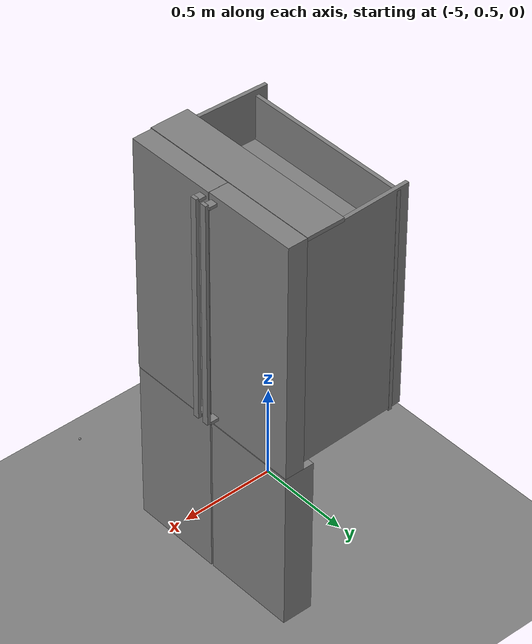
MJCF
<mujoco>
    <option gravity="0.000000000 0.000000000 -9.810000420" timestep="0.0049999999" integrator="implicitfast" density="1.225" viscosity="1.8000001e-05" noslip_iterations="10" iterations="100" sdf_iterations="50">
        <flag multiccd="disable"/>
    </option>
    <size memory="1000M"/>
    <compiler coordinate="local"/>
    <worldbody>
        <light cutoff="30" pos="0 1 1" dir="0 -1 -2"/>
        <light cutoff="30" pos="0 -1 1" dir="0 1 -2"/>
        <body pos="-4.455995083 0.348160446 1.533870339" euler="0.000000000 0.000000000 0.000000000" name="openloong_gripper_2f85_fix_base_usda_fridge_left_up">
            <geom contype="1" conaffinity="1" density="1000" type="box" material="" rgba="0.500000000 0.500000000 0.500000000 1.000000000" solimp="0.899999976 0.949999988 0.001000000" friction="1.000000000 0.005000000 0.000100000" solref="0.020000000 1.000000000" margin="0" condim="3" group="0" pos="0.034918308 0.246351242 -0.000000358" quat="1.000000000 0.000000000 0.000000000 0.000013381" size="0.052000001 0.243000001 0.625000000" name="openloong_gripper_2f85_fix_base_usda_Fridge_02_a_62515249_83F1_46ED_9A18_1D3F6E66D0CC"/>
            <geom contype="1" conaffinity="1" density="1000" type="box" material="" rgba="0.500000000 0.500000000 0.500000000 1.000000000" solimp="0.899999976 0.949999988 0.001000000" friction="1.000000000 0.005000000 0.000100000" solref="0.020000000 1.000000000" margin="0" condim="3" group="0" pos="-0.055340290 0.240164995 -0.197626591" quat="0.999999940 0.000000000 0.000000000 0.000271916" size="0.035000000 0.200000003 0.075999998" name="openloong_gripper_2f85_fix_base_usda_Fridge_02_g_1500D9E5_1739_44AF_BB22_A192F1814C3C"/>
            <geom contype="1" conaffinity="1" density="1000" type="box" material="" rgba="0.500000000 0.500000000 0.500000000 1.000000000" solimp="0.899999976 0.949999988 0.001000000" friction="1.000000000 0.005000000 0.000100000" solref="0.020000000 1.000000000" margin="0" condim="3" group="0" pos="-0.036716461 0.240169704 0.099823833" quat="1.000000000 0.000000000 0.000000000 0.000120342" size="0.020000000 0.200000003 0.070000000" name="openloong_gripper_2f85_fix_base_usda_Fridge_02_f_85114951_267C_4593_B382_A97FD6771417"/>
            <geom contype="1" conaffinity="1" density="1000" type="box" material="" rgba="0.500000000 0.500000000 0.500000000 1.000000000" solimp="0.899999976 0.949999988 0.001000000" friction="1.000000000 0.005000000 0.000100000" solref="0.020000000 1.000000000" margin="0" condim="3" group="0" pos="0.133846283 0.458910882 0.011316895" quat="1.000000000 0.000000000 0.000000000 0.000000417" size="0.008500000 0.016000001 0.595000029" name="openloong_gripper_2f85_fix_base_usda_Fridge_02_b_1A1AB566_64D7_4F22_AA23_7B2DF2EF20AC"/>
            <geom contype="1" conaffinity="1" density="1000" type="box" material="" rgba="0.500000000 0.500000000 0.500000000 1.000000000" solimp="0.899999976 0.949999988 0.001000000" friction="1.000000000 0.005000000 0.000100000" solref="0.020000000 1.000000000" margin="0" condim="3" group="0" pos="-0.036197186 0.240169704 0.373237491" quat="1.000000000 0.000000000 0.000000000 0.000087470" size="0.020000000 0.200000003 0.070000000" name="openloong_gripper_2f85_fix_base_usda_Fridge_02_e_470E68C5_8A9F_49D3_8487_AA3706A3BE13"/>
            <geom contype="1" conaffinity="1" density="1000" type="box" material="" rgba="0.500000000 0.500000000 0.500000000 1.000000000" solimp="0.899999976 0.949999988 0.001000000" friction="1.000000000 0.005000000 0.000100000" solref="0.020000000 1.000000000" margin="0" condim="3" group="0" pos="0.097751617 0.454878092 -0.576283276" quat="1.000000000 0.000000000 0.000000000 0.000000417" size="0.029999999 0.018999999 0.008000000" name="openloong_gripper_2f85_fix_base_usda_Fridge_02_c_0AF45024_51F9_4909_99F1_C3CD49CDD27A"/>
            <geom contype="1" conaffinity="1" density="1000" type="box" material="" rgba="0.500000000 0.500000000 0.500000000 1.000000000" solimp="0.899999976 0.949999988 0.001000000" friction="1.000000000 0.005000000 0.000100000" solref="0.020000000 1.000000000" margin="0" condim="3" group="0" pos="0.096112251 0.454878092 0.589555621" quat="1.000000000 0.000000000 0.000000000 0.000000417" size="0.029999999 0.018999999 0.008000000" name="openloong_gripper_2f85_fix_base_usda_Fridge_02_d_1FA14AA6_3118_4843_B926_7F7168E1C658"/>
            <joint armature="0" stiffness="0" damping="5" axis="0.000000 0.000000 -1.000000" limited="true" range="0.000000000 180.000000000" type="hinge" name="openloong_gripper_2f85_fix_base_usda_fridge_left_up_joint"/>
        </body>
        <body pos="-4.456572533 1.328142047 1.533870339" euler="0.000000000 0.000000000 0.000000000" name="openloong_gripper_2f85_fix_base_usda_fridge_right_up">
            <geom contype="1" conaffinity="1" density="1000" type="box" material="" rgba="0.500000000 0.500000000 0.500000000 1.000000000" solimp="0.899999976 0.949999988 0.001000000" friction="1.000000000 0.005000000 0.000100000" solref="0.020000000 1.000000000" margin="0" condim="3" group="0" pos="-0.042358875 -0.244417667 0.003658533" quat="0.999999881 0.000000000 0.000000000 0.000160277" size="0.020000000 0.189999998 0.500000000" name="openloong_gripper_2f85_fix_base_usda_geom_E2D0C84D_484F_4AED_89BE_614D011CD84C"/>
            <geom contype="1" conaffinity="1" density="1000" type="box" material="" rgba="0.500000000 0.500000000 0.500000000 1.000000000" solimp="0.899999976 0.949999988 0.001000000" friction="1.000000000 0.005000000 0.000100000" solref="0.020000000 1.000000000" margin="0" condim="3" group="0" pos="0.134432793 -0.461116314 0.011315942" quat="0.999999940 0.000000075 -0.000000089 0.000017196" size="0.008500000 0.016000001 0.595000029" name="openloong_gripper_2f85_fix_base_usda_geom_AE1C807B_DBF7_4810_96EB_FE9989117805"/>
            <geom contype="1" conaffinity="1" density="1000" type="box" material="" rgba="0.500000000 0.500000000 0.500000000 1.000000000" solimp="0.899999976 0.949999988 0.001000000" friction="1.000000000 0.005000000 0.000100000" solref="0.020000000 1.000000000" margin="0" condim="3" group="0" pos="0.096698761 -0.456393361 0.589552999" quat="0.999999881 0.000000074 -0.000000089 0.000032246" size="0.029999999 0.018999999 0.008000000" name="openloong_gripper_2f85_fix_base_usda_geom_AE89DBAE_7A61_4667_B888_9C59EEF22AA3"/>
            <geom contype="1" conaffinity="1" density="1000" type="box" material="" rgba="0.500000000 0.500000000 0.500000000 1.000000000" solimp="0.899999976 0.949999988 0.001000000" friction="1.000000000 0.005000000 0.000100000" solref="0.020000000 1.000000000" margin="0" condim="3" group="0" pos="0.098338127 -0.456895828 -0.576284051" quat="0.999999940 0.000000074 -0.000000089 0.000029832" size="0.029999999 0.018999999 0.008000000" name="openloong_gripper_2f85_fix_base_usda_geom_AB835C0C_0D5A_42C1_99F6_9B830FCD44ED"/>
            <geom contype="1" conaffinity="1" density="1000" type="box" material="" rgba="0.500000000 0.500000000 0.500000000 1.000000000" solimp="0.899999976 0.949999988 0.001000000" friction="1.000000000 0.005000000 0.000100000" solref="0.020000000 1.000000000" margin="0" condim="3" group="0" pos="0.034286022 -0.245587349 0.000602603" quat="0.999999881 0.000000000 0.000000000 0.000051796" size="0.050999999 0.243000001 0.625000000" name="openloong_gripper_2f85_fix_base_usda_geom_8F8683B2_3204_4080_A304_B4C07A5ED43F"/>
            <joint armature="0" stiffness="0" damping="5" axis="0.000000 0.000000 1.000000" limited="true" range="0.000000000 180.000000000" type="hinge" name="openloong_gripper_2f85_fix_base_usda_fridge_right_up_joint"/>
        </body>
        <body pos="0.000000000 0.000000000 0.000000000" euler="0.000000000 0.000000000 0.000000000" name="StaticObjcets_StaticObjcets">
            <geom contype="2" conaffinity="2" density="1000" type="box" material="" rgba="0.500000000 0.500000000 0.500000000 1.000000000" solimp="0.899999976 0.949999988 0.001000000" friction="1.000000000 0.005000000 0.000100000" solref="0.020000000 1.000000000" margin="0" condim="3" group="0" pos="-4.761908531 0.835612714 1.871172667" quat="1.000000000 0.000000000 0.000000000 0.000000000" size="0.250000000 0.439999998 0.005000000" name="StaticObjcets_geom_17513207_3133_47FF_879F_DE6E8514283A"/>
            <geom contype="2" conaffinity="2" density="1000" type="box" material="" rgba="0.500000000 0.500000000 0.500000000 1.000000000" solimp="0.899999976 0.949999988 0.001000000" friction="1.000000000 0.005000000 0.000100000" solref="0.020000000 1.000000000" margin="0" condim="3" group="0" pos="-4.769333839 0.386707336 1.535037637" quat="0.707029462 0.707027197 -0.010532650 -0.010532619" size="0.300000012 0.600000024 0.010000000" name="StaticObjcets_geom_C5B9DAB3_21C2_4AEF_9549_185F0784ED24"/>
            <geom contype="2" conaffinity="2" density="1000" type="box" material="" rgba="0.500000000 0.500000000 0.500000000 1.000000000" solimp="0.899999976 0.949999988 0.001000000" friction="1.000000000 0.005000000 0.000100000" solref="0.020000000 1.000000000" margin="0" condim="3" group="0" pos="-4.763467789 0.835180044 1.691508532" quat="1.000000000 0.000000000 0.000000000 0.000000000" size="0.250000000 0.439999998 0.005000000" name="StaticObjcets_geom_682F2336_C7B6_4477_A25E_A48205D1E2FC"/>
            <geom contype="2" conaffinity="2" density="1000" type="box" material="" rgba="0.500000000 0.500000000 0.500000000 1.000000000" solimp="0.899999976 0.949999988 0.001000000" friction="1.000000000 0.005000000 0.000100000" solref="0.020000000 1.000000000" margin="0" condim="3" group="0" pos="-4.454798698 1.079833508 0.470532238" quat="0.707107067 0.000000000 0.000000000 0.707106471" size="0.239999995 0.079999998 0.430000007" name="StaticObjcets_Fridge_03_C08DC559_8D2B_4AE3_8008_7E632653AEE5"/>
            <geom contype="1" conaffinity="1" density="1000" type="plane" material="" rgba="0.500000000 0.500000000 0.500000000 1.000000000" solimp="0.899999976 0.949999988 0.001000000" friction="1.000000000 0.005000000 0.000100000" solref="0.020000000 1.000000000" margin="0" condim="3" group="0" pos="-0.043989260 0.222946882 0.032030921" quat="1.000000000 0.000000000 0.000000000 0.000000000" size="8.000000000 8.000000000 1.000000000" name="StaticObjcets_geom_BD786E4D_5416_4B03_BC1F_B1A3E6C47686"/>
            <geom contype="2" conaffinity="2" density="1000" type="box" material="" rgba="0.500000000 0.500000000 0.500000000 1.000000000" solimp="0.899999976 0.949999988 0.001000000" friction="1.000000000 0.005000000 0.000100000" solref="0.020000000 1.000000000" margin="0" condim="3" group="0" pos="-4.771282196 1.281533480 1.516736507" quat="0.707029462 0.707027197 0.010532652 0.010532617" size="0.300000012 0.600000024 0.010000000" name="StaticObjcets_geom_A7BD61A3_111F_4188_A04C_56885F059FB0"/>
            <geom contype="2" conaffinity="2" density="1000" type="box" material="" rgba="0.500000000 0.500000000 0.500000000 1.000000000" solimp="0.899999976 0.949999988 0.001000000" friction="1.000000000 0.005000000 0.000100000" solref="0.020000000 1.000000000" margin="0" condim="3" group="0" pos="-4.765080929 0.836613894 1.500948071" quat="1.000000000 0.000000000 0.000000000 0.000000000" size="0.250000000 0.439999998 0.005000000" name="StaticObjcets_geom_A29EDA16_D4DE_4B5E_9693_47C61FBB469E"/>
            <geom contype="2" conaffinity="2" density="1000" type="box" material="" rgba="0.500000000 0.500000000 0.500000000 1.000000000" solimp="0.899999976 0.949999988 0.001000000" friction="1.000000000 0.005000000 0.000100000" solref="0.020000000 1.000000000" margin="0" condim="3" group="0" pos="-4.717486858 0.835144579 1.096694350" quat="1.000000000 0.000000000 0.000000000 0.000000000" size="0.200000003 0.439999998 0.119999997" name="StaticObjcets_geom_F79D0C10_AEBE_486D_9F08_A86D2AA63312"/>
            <geom contype="2" conaffinity="2" density="1000" type="box" material="" rgba="0.500000000 0.500000000 0.500000000 1.000000000" solimp="0.899999976 0.949999988 0.001000000" friction="1.000000000 0.005000000 0.000100000" solref="0.020000000 1.000000000" margin="0" condim="3" group="0" pos="-4.453287601 0.590693057 0.470532209" quat="0.707107067 0.000000000 0.000000000 0.707106471" size="0.239999995 0.079999998 0.430000007" name="StaticObjcets_Fridge_04_a_FC5BCB95_979B_4443_94FF_E8B6FBE87264"/>
            <geom contype="1" conaffinity="1" density="1000" type="box" material="" rgba="0.500000000 0.500000000 0.500000000 1.000000000" solimp="0.899999976 0.949999988 0.001000000" friction="1.000000000 0.005000000 0.000100000" solref="0.020000000 1.000000000" margin="0" condim="3" group="0" pos="-4.573544502 0.835462213 2.151423454" quat="1.000000000 0.000000000 0.000000000 0.000000000" size="0.100000001 0.490000010 0.010000000" name="StaticObjcets_geom_56697DE3_CC12_4A3D_8D3F_3A77A27071C1"/>
            <geom contype="2" conaffinity="2" density="1000" type="box" material="" rgba="0.500000000 0.500000000 0.500000000 1.000000000" solimp="0.899999976 0.949999988 0.001000000" friction="1.000000000 0.005000000 0.000100000" solref="0.020000000 1.000000000" margin="0" condim="3" group="0" pos="-5.012205601 0.835292637 1.504703879" quat="0.500000417 0.499999970 0.499999970 0.499999553" size="0.449999988 0.600000024 0.010000000" name="StaticObjcets_Fridge_only_08_E2FA04FC_E302_498A_803A_A009F3D7D652"/>
        </body>
        <body pos="-3.933782578 0.870087445 2.384232044" euler="-124.244743347 -38.702983856 -22.827419281" mocap="true" name="spotlight2_SpotLight"/>
        <body pos="-4.075227737 0.392798066 2.383229017" euler="148.060913086 -55.771587372 -4.302770615" mocap="true" name="spotlight5_SpotLight"/>
        <body pos="-3.768655777 1.090464473 2.379599094" euler="-119.575500488 -47.158058167 -161.846740723" mocap="true" name="spotlight3_SpotLight"/>
        <body pos="-3.662749529 0.835145235 0.026324987" euler="0.000000000 0.000000000 180.000000000" mocap="true" name="openloong_gripper_2f85_fix_base_usda_leftHandMocap"/>
        <body pos="-3.662749529 0.835145235 0.026324987" euler="0.000000000 0.000000000 180.000000000" mocap="true" name="openloong_gripper_2f85_fix_base_usda_rightHandMocap"/>
        <body pos="-3.662749529 0.835145235 1.226325035" euler="0.000000000 0.000000000 180.000000000" name="openloong_gripper_2f85_fix_base_usda_base_link">
            <geom contype="1" conaffinity="1" density="1000" type="mesh" material="" rgba="0.783999979 0.783999979 0.783999979 1.000000000" solimp="0.899999976 0.949999988 0.001000000" friction="1.000000000 0.005000000 0.000100000" solref="0.020000000 1.000000000" margin="0" condim="3" group="3" mesh="base_link" pos="0.000000000 0.000000000 0.000000000" quat="1.000000000 0.000000000 0.000000000 0.000000000" size="1.000000000 1.000000000 1.000000000" name="openloong_gripper_2f85_fix_base_usda__geom_7_599A3A5F_1884_4D48_AC69_7FBBBA53AF99"/>
            <site size="0.005000000 0.005000000 0.005000000" rgba="0.500000000 0.500000000 0.500000000 1.000000000" pos="0.000000000 0.000000000 0.000000000" quat="1.000000000 0.000000000 0.000000000 0.000000000" group="0" type="sphere" name="openloong_gripper_2f85_fix_base_usda_imu"/>
            <inertial mass="22.447001" pos="-0.005664100 -0.001336700 0.238289997" diaginertia="0.374352545 0.277180195 0.220617250" quat="0.999247074 0.035235517 -0.015086859 0.006023135"/>
            <body pos="0.000000000 0.000000000 0.299999952" euler="0.000000000 0.000000000 0.000000000" name="openloong_gripper_2f85_fix_base_usda_dummy_body">
                <geom contype="1" conaffinity="1" density="1000" type="sphere" material="" rgba="0.783999979 0.783999979 0.783999979 1.000000000" solimp="0.899999976 0.949999988 0.001000000" friction="1.000000000 0.005000000 0.000100000" solref="0.020000000 1.000000000" margin="0" condim="3" group="3" pos="0.000000000 0.000000000 0.000000000" quat="1.000000000 0.000000000 0.000000000 0.000000000" size="0.010000000 0.000000000 0.000000000" name="openloong_gripper_2f85_fix_base_usda__geom_8_B2D5A664_ED1A_482D_B2B7_B6C5C50C0355"/>
                <joint armature="0.0099999998" stiffness="0" damping="0.1" axis="0.000000 0.000000 1.000000" type="hinge" name="openloong_gripper_2f85_fix_base_usda_dummy_joint"/>
                <site size="0.010000000 0.005000000 0.005000000" rgba="0.500000000 0.500000000 0.500000000 1.000000000" pos="0.000000000 0.000000000 0.000000000" quat="1.000000000 0.000000000 0.000000000 0.000000000" group="3" type="sphere" name="openloong_gripper_2f85_fix_base_usda_dummy_site"/>
            </body>
            <body pos="0.009000063 0.000000000 0.406399965" euler="0.000000000 0.000000000 0.000000000" name="openloong_gripper_2f85_fix_base_usda_Link_head_yaw">
                <geom contype="1" conaffinity="1" density="1000" type="mesh" material="" rgba="0.783999979 0.783999979 0.783999979 1.000000000" solimp="0.899999976 0.949999988 0.001000000" friction="1.000000000 0.005000000 0.000100000" solref="0.020000000 1.000000000" margin="0" condim="3" group="3" mesh="Link_head_yaw" pos="0.000000000 0.000000000 0.000000000" quat="1.000000000 0.000000000 0.000000000 0.000000000" size="1.000000000 1.000000000 1.000000000" name="openloong_gripper_2f85_fix_base_usda__geom_10_1A523895_1456_4015_B651_8F99A3DD59E3"/>
                <inertial mass="0.84249002" pos="0.000000000 -0.002081400 0.044801001" diaginertia="0.000700588 0.000629000 0.000553812" quat="0.706933022 -0.015675601 0.015677100 0.706933022"/>
                <body pos="0.000000000 -0.034600019 0.048500061" euler="0.000000000 0.000000000 0.000000000" name="openloong_gripper_2f85_fix_base_usda_Link_head_pitch">
                    <geom contype="1" conaffinity="1" density="1000" type="mesh" material="" rgba="0.783999979 0.783999979 0.783999979 1.000000000" solimp="0.899999976 0.949999988 0.001000000" friction="1.000000000 0.005000000 0.000100000" solref="0.020000000 1.000000000" margin="0" condim="3" group="3" mesh="Link_head_pitch" pos="0.000000000 0.000000000 0.000000000" quat="1.000000000 0.000000000 0.000000000 0.000000000" size="1.000000000 1.000000000 1.000000000" name="openloong_gripper_2f85_fix_base_usda__geom_12_40BB5703_D56D_447F_99B9_C29A48869323"/>
                    <inertial mass="1.3943" pos="0.020569000 0.033004001 0.125000000" diaginertia="0.006381400 0.006289940 0.004481460" quat="0.973390222 0.008406822 0.228157058 0.019624906"/>
                    <body pos="0.000000000 0.029999971 0.000000000" euler="0.000000000 0.000000000 0.000000000" name="openloong_gripper_2f85_fix_base_usda_neck_center_body">
                        <site size="0.010000000 0.005000000 0.005000000" rgba="0.500000000 0.500000000 0.500000000 1.000000000" pos="0.000000000 0.000000000 0.000000000" quat="1.000000000 0.000000000 0.000000000 0.000000000" group="3" type="sphere" name="openloong_gripper_2f85_fix_base_usda_neck_center_site"/>
                        <body pos="0.019999981 0.000000000 0.149999976" euler="-0.000002229 39.998176575 -90.000205994" name="openloong_gripper_2f85_fix_base_usda_camera_head">
                            <site size="0.010000000 0.005000000 0.005000000" rgba="0.500000000 0.500000000 0.500000000 1.000000000" pos="0.000000000 0.000000000 0.000000000" quat="1.000000000 0.000000000 0.000000000 0.000000000" group="3" type="sphere" name="openloong_gripper_2f85_fix_base_usda_camera_head_site"/>
                        </body>
                    </body>
                </body>
            </body>
            <body pos="0.003999949 -0.161599994 0.392199993" euler="0.000000000 0.000000000 0.000000000" name="openloong_gripper_2f85_fix_base_usda_Link_arm_r_01">
                <geom contype="1" conaffinity="1" density="1000" type="mesh" material="" rgba="0.783999979 0.783999979 0.783999979 1.000000000" solimp="0.899999976 0.949999988 0.001000000" friction="1.000000000 0.005000000 0.000100000" solref="0.020000000 1.000000000" margin="0" condim="3" group="3" mesh="Link_arm_r_01" pos="0.000000000 0.000000000 0.000000000" quat="1.000000000 0.000000000 0.000000000 0.000000000" size="1.000000000 1.000000000 1.000000000" name="openloong_gripper_2f85_fix_base_usda__geom_14_916F725E_B489_47B1_9423_D0B6A828ABDC"/>
                <joint armature="0.0099999998" stiffness="0" damping="1" axis="0.000000 -1.000000 0.000000" limited="true" range="-170.000015259 170.000015259" type="hinge" name="openloong_gripper_2f85_fix_base_usda_J_arm_r_01"/>
                <inertial mass="0.75641" pos="0.004494600 -0.038293999 -0.000001874" diaginertia="0.000842990 0.000803050 0.000587120" quat="-0.000163502 0.707098067 0.000812463 0.707115054"/>
                <body pos="-0.042000055 -0.041000009 0.000000000" euler="0.000000000 0.000000000 0.000000000" name="openloong_gripper_2f85_fix_base_usda_Link_arm_r_02">
                    <geom contype="1" conaffinity="1" density="1000" type="mesh" material="" rgba="0.783999979 0.783999979 0.783999979 1.000000000" solimp="0.899999976 0.949999988 0.001000000" friction="1.000000000 0.005000000 0.000100000" solref="0.020000000 1.000000000" margin="0" condim="3" group="3" mesh="Link_arm_r_02" pos="0.000000000 0.000000000 0.000000000" quat="1.000000000 0.000000000 0.000000000 0.000000000" size="1.000000000 1.000000000 1.000000000" name="openloong_gripper_2f85_fix_base_usda__geom_16_277594DB_8088_4D1F_9598_19B3794568F5"/>
                    <joint armature="0.0099999998" stiffness="0" damping="1" axis="-1.000000 0.000000 0.000000" limited="true" range="-105.000244141 105.000244141" type="hinge" name="openloong_gripper_2f85_fix_base_usda_J_arm_r_02"/>
                    <inertial mass="0.98500001" pos="0.041999999 -0.067430697 0.000000000" diaginertia="0.002262690 0.001730990 0.001154020" quat="0.500000000 0.500000000 -0.500000000 0.500000000"/>
                    <body pos="0.042000055 -0.122599959 0.000000000" euler="0.000000000 0.000000000 0.000000000" name="openloong_gripper_2f85_fix_base_usda_Link_arm_r_03">
                        <geom contype="1" conaffinity="1" density="1000" type="mesh" material="" rgba="0.783999979 0.783999979 0.783999979 1.000000000" solimp="0.899999976 0.949999988 0.001000000" friction="1.000000000 0.005000000 0.000100000" solref="0.020000000 1.000000000" margin="0" condim="3" group="3" mesh="Link_arm_r_03" pos="0.000000000 0.000000000 0.000000000" quat="1.000000000 0.000000000 0.000000000 0.000000000" size="1.000000000 1.000000000 1.000000000" name="openloong_gripper_2f85_fix_base_usda__geom_18_17208835_5D88_40DD_BBD8_2591EDD19DF6"/>
                        <joint armature="0.0099999998" stiffness="0" damping="1" axis="0.000000 -1.000000 0.000000" limited="true" range="-170.000015259 170.000015259" type="hinge" name="openloong_gripper_2f85_fix_base_usda_J_arm_r_03"/>
                        <inertial mass="0.95899999" pos="-0.001413580 -0.164663002 0.020757901" diaginertia="0.002101340 0.002064590 0.000754802" quat="0.560480952 0.454391927 -0.443732947 0.531497955"/>
                        <body pos="0.035300016 -0.177399993 0.024000049" euler="0.000000000 0.000000000 0.000000000" name="openloong_gripper_2f85_fix_base_usda_Link_arm_r_04">
                            <geom contype="1" conaffinity="1" density="1000" type="mesh" material="" rgba="0.783999979 0.783999979 0.783999979 1.000000000" solimp="0.899999976 0.949999988 0.001000000" friction="1.000000000 0.005000000 0.000100000" solref="0.020000000 1.000000000" margin="0" condim="3" group="3" mesh="Link_arm_r_04" pos="0.000000000 0.000000000 0.000000000" quat="1.000000000 0.000000000 0.000000000 0.000000000" size="1.000000000 1.000000000 1.000000000" name="openloong_gripper_2f85_fix_base_usda__geom_20_C65B6AFD_474E_4C51_A35F_D61BDDB5B172"/>
                            <joint armature="0.0099999998" stiffness="0" damping="1" axis="-1.000000 0.000000 0.000000" limited="true" range="0.000000000 170.000015259" type="hinge" name="openloong_gripper_2f85_fix_base_usda_J_arm_r_04"/>
                            <inertial mass="0.60000002" pos="-0.038727000 -0.060766999 -0.021003000" diaginertia="0.001092610 0.000712422 0.000645102" quat="0.327701002 0.632602990 -0.467366993 0.523443997"/>
                            <body pos="-0.035300016 -0.103500009 -0.024000049" euler="0.000000000 0.000000000 0.000000000" name="openloong_gripper_2f85_fix_base_usda_Link_arm_r_05">
                                <geom contype="1" conaffinity="1" density="1000" type="mesh" material="" rgba="0.783999979 0.783999979 0.783999979 1.000000000" solimp="0.899999976 0.949999988 0.001000000" friction="1.000000000 0.005000000 0.000100000" solref="0.020000000 1.000000000" margin="0" condim="3" group="3" mesh="Link_arm_r_05" pos="0.000000000 0.000000000 0.000000000" quat="1.000000000 0.000000000 0.000000000 0.000000000" size="1.000000000 1.000000000 1.000000000" name="openloong_gripper_2f85_fix_base_usda__geom_22_8F25E610_327C_44EB_905B_30683AE8A0A4"/>
                                <joint armature="0.0099999998" stiffness="0" damping="1" axis="0.000000 -1.000000 0.000000" limited="true" range="-170.000015259 170.000015259" type="hinge" name="openloong_gripper_2f85_fix_base_usda_J_arm_r_05"/>
                                <inertial mass="0.68976003" pos="0.000032712 -0.068658002 -0.000111780" diaginertia="0.002522510 0.002411100 0.000448695" quat="0.707660973 0.706543028 -0.002603360 0.002470550"/>
                                <body pos="-0.026499987 -0.196499944 0.000000000" euler="0.000000000 0.000000000 0.000000000" name="openloong_gripper_2f85_fix_base_usda_Link_arm_r_06">
                                    <geom contype="1" conaffinity="1" density="1000" type="mesh" material="" rgba="0.783999979 0.783999979 0.783999979 1.000000000" solimp="0.899999976 0.949999988 0.001000000" friction="1.000000000 0.005000000 0.000100000" solref="0.020000000 1.000000000" margin="0" condim="3" group="3" mesh="Link_arm_r_06" pos="0.000000000 0.000000000 0.000000000" quat="1.000000000 0.000000000 0.000000000 0.000000000" size="1.000000000 1.000000000 1.000000000" name="openloong_gripper_2f85_fix_base_usda__geom_24_9873C08E_B8CD_4E42_962E_355EC46DD536"/>
                                    <joint armature="0.0099999998" stiffness="0" damping="1" axis="1.000000 0.000000 0.000000" limited="true" range="-105.000244141 105.000244141" type="hinge" name="openloong_gripper_2f85_fix_base_usda_J_arm_r_06"/>
                                    <inertial mass="0.28" pos="0.026078001 -0.000000896 0.001663700" diaginertia="0.000156930 0.000145601 0.000104979" quat="0.707080841 0.001851080 0.001883810 0.707127810"/>
                                    <body pos="0.026499987 0.000000000 0.031800032" euler="0.000000000 0.000000000 0.000000000" name="openloong_gripper_2f85_fix_base_usda_Link_arm_r_07">
                                        <geom contype="1" conaffinity="1" density="1000" type="mesh" material="" rgba="0.783999979 0.783999979 0.783999979 1.000000000" solimp="0.899999976 0.949999988 0.001000000" friction="1.000000000 0.005000000 0.000100000" solref="0.020000000 1.000000000" margin="0" condim="3" group="3" mesh="Link_arm_r_07" pos="0.000000000 0.000000000 0.000000000" quat="1.000000000 0.000000000 0.000000000 0.000000000" size="1.000000000 1.000000000 1.000000000" name="openloong_gripper_2f85_fix_base_usda__geom_26_81A07EC1_844C_4444_B718_4F00F2F71C6D"/>
                                        <joint armature="0.0099999998" stiffness="0" damping="1" axis="0.000000 0.000000 1.000000" limited="true" range="-60.000133514 60.000133514" type="hinge" name="openloong_gripper_2f85_fix_base_usda_J_arm_r_07"/>
                                        <inertial mass="0.61353999" pos="-0.007859000 -0.158170000 -0.027736001" diaginertia="0.003037610 0.002570910 0.000729379" quat="0.427542925 0.443532884 -0.553093910 0.560867906"/>
                                        <body pos="0.000000000 0.286999941 -0.269999981" euler="150.000350952 0.000000000 0.000000000" name="openloong_gripper_2f85_fix_base_usda_camera_wrist_r">
                                            <site size="0.010000000 0.005000000 0.005000000" rgba="0.500000000 0.500000000 0.500000000 1.000000000" pos="0.000000000 0.000000000 0.000000000" quat="1.000000000 0.000000000 0.000000000 0.000000000" group="3" type="sphere" name="openloong_gripper_2f85_fix_base_usda_camera_wrist_r_site"/>
                                        </body>
                                        <body pos="0.000000000 -0.220000029 -0.032999992" euler="0.000000000 0.000000000 179.999969482" name="openloong_gripper_2f85_fix_base_usda_ee_center_body_r">
                                            <site size="0.010000000 0.005000000 0.005000000" rgba="0.500000000 0.500000000 0.500000000 1.000000000" pos="0.000000000 0.000000000 0.000000000" quat="1.000000000 0.000000000 0.000000000 0.000000000" group="3" type="sphere" name="openloong_gripper_2f85_fix_base_usda_ee_center_site_r"/>
                                        </body>
                                        <body pos="0.000000000 -0.065999985 -0.031000018" euler="89.999984741 0.000000000 180.000000000" name="openloong_gripper_2f85_fix_base_usda_zbr_base_link">
                                            <geom contype="1" conaffinity="1" density="1000" type="mesh" material="" rgba="0.783999979 0.783999979 0.783999979 1.000000000" solimp="0.899999976 0.949999988 0.001000000" friction="1.000000000 0.005000000 0.000100000" solref="0.020000000 1.000000000" margin="0" condim="3" group="3" mesh="base" pos="0.000000000 0.000000000 0.000000000" quat="1.000000000 0.000000000 0.000000000 0.000000000" size="1.000000238 1.000000238 1.000000238" name="openloong_gripper_2f85_fix_base_usda__geom_30_ED3454DC_5237_4F97_B8EC_707D07FA0ADA"/>
                                            <inertial mass="0.77744102" pos="0.000000000 -0.000027039 0.035467502" diaginertia="0.000260285 0.000225381 0.000152708" quat="0.999998808 -0.001528488 0.000000000 0.000000000"/>
                                            <body pos="-0.030601032 0.004750133 0.065704480" euler="-89.999977112 0.000000000 0.000000000" name="openloong_gripper_2f85_fix_base_usda_r_left_driver">
                                                <geom contype="1" conaffinity="1" density="1000" type="mesh" material="" rgba="0.783999979 0.783999979 0.783999979 1.000000000" solimp="0.899999976 0.949999988 0.001000000" friction="1.000000000 0.005000000 0.000100000" solref="0.020000000 1.000000000" margin="0" condim="3" group="3" mesh="driver" pos="0.030601032 0.054904357 -0.004699946" quat="0.707106709 0.707106590 0.000000000 0.000000000" size="1.000000238 1.000000238 1.000000238" name="openloong_gripper_2f85_fix_base_usda__geom_32_D5573D94_AC9A_4F2E_83FF_C271208C4EAC"/>
                                                <joint armature="0.0049999999" stiffness="0" damping="0.1" axis="0.000000 0.000000 1.000000" limited="true" range="0.000000000 51.566200256" type="hinge" name="openloong_gripper_2f85_fix_base_usda_r_left_driver_joint"/>
                                                <inertial mass="0.0089956298" pos="0.000000000 0.017754700 0.001073140" diaginertia="0.000001724 0.000001609 0.000000322" quat="0.681301236 0.732003212 0.000000000 0.000000000"/>
                                                <body pos="-0.031425007 0.004532219 -0.010200026" euler="0.000000000 0.000000000 180.000000000" name="openloong_gripper_2f85_fix_base_usda_r_left_coupler">
                                                    <geom contype="1" conaffinity="1" density="1000" type="mesh" material="" rgba="0.783999979 0.783999979 0.783999979 1.000000000" solimp="0.899999976 0.949999988 0.001000000" friction="1.000000000 0.005000000 0.000100000" solref="0.020000000 1.000000000" margin="0" condim="3" group="3" mesh="coupler" pos="-0.062026039 -0.050372254 0.005499960" quat="0.707106709 -0.707106590 0.000000000 0.000000000" size="1.000000238 1.000000238 1.000000238" name="openloong_gripper_2f85_fix_base_usda__geom_34_4597399C_FC96_4DD2_850C_AD61778FB1B3"/>
                                                    <inertial mass="0.0140974" pos="0.000000000 0.003012090 0.023217499" diaginertia="0.000004162 0.000003522 0.000000888" quat="0.705635548 -0.045590367 0.045590367 0.705635548"/>
                                                </body>
                                            </body>
                                            <body pos="-0.012700084 -0.011999848 0.072219983" euler="-89.999977112 0.000000000 0.000000000" name="openloong_gripper_2f85_fix_base_usda_r_left_spring_link">
                                                <geom contype="1" conaffinity="1" density="1000" type="mesh" material="" rgba="0.783999979 0.783999979 0.783999979 1.000000000" solimp="0.899999976 0.949999988 0.001000000" friction="1.000000000 0.005000000 0.000100000" solref="0.020000000 1.000000000" margin="0" condim="3" group="3" mesh="spring_link" pos="0.012700084 0.061419860 0.012050035" quat="0.707106709 0.707106590 0.000000000 0.000000000" size="1.000000238 1.000000238 1.000000238" name="openloong_gripper_2f85_fix_base_usda__geom_36_C81D2322_CDD5_4D30_8B4A_3C7BD8B88DCB"/>
                                                <joint armature="0.001" stiffness="0.050000001" damping="0.00125" axis="0.000000 0.000000 1.000000" limited="true" range="-17.000000000 51.566200256" type="hinge" name="openloong_gripper_2f85_fix_base_usda_r_left_spring_link_joint"/>
                                                <inertial mass="0.0221642" pos="-0.000000009 0.018162400 0.021265799" diaginertia="0.000008969 0.000006717 0.000002639" quat="0.663403213 -0.244737089 0.244737089 0.663403213"/>
                                                <body pos="-0.038208015 -0.042500269 0.002950073" euler="180.000000000 0.000000000 -0.002179886" name="openloong_gripper_2f85_fix_base_usda_r_left_follower">
                                                    <geom contype="1" conaffinity="1" density="1000" type="mesh" material="" rgba="0.783999979 0.783999979 0.783999979 1.000000000" solimp="0.899999976 0.949999988 0.001000000" friction="1.000000000 0.005000000 0.000100000" solref="0.020000000 1.000000000" margin="0" condim="3" group="3" mesh="follower" pos="0.050907861 -0.103919886 -0.009099962" quat="0.707106709 -0.707106590 0.000000000 -0.000000000" size="1.000000238 1.000000238 1.000000238" name="openloong_gripper_2f85_fix_base_usda__geom_39_C553B578_B7BC_475A_B1C6_938F92796620"/>
                                                    <geom contype="1" conaffinity="1" density="1000" type="mesh" material="" rgba="0.783999979 0.783999979 0.783999979 1.000000000" solimp="0.899999976 0.949999988 0.001000000" friction="1.000000000 0.005000000 0.000100000" solref="0.020000000 1.000000000" margin="0" condim="3" group="3" mesh="tongue" pos="0.050907861 -0.103919886 -0.009099962" quat="0.707106709 -0.707106590 0.000000000 -0.000000000" size="1.000000238 1.000000238 1.000000238" name="openloong_gripper_2f85_fix_base_usda__geom_40_0BD77EB5_F6F7_4034_8396_C1894DEC4B7E"/>
                                                    <joint armature="0.001" stiffness="0" damping="0.1" axis="0.000000 0.000000 1.000000" limited="true" range="-49.999961853 51.566200256" type="hinge" name="openloong_gripper_2f85_fix_base_usda_r_left_follower"/>
                                                    <inertial mass="0.0125222" pos="0.000000000 -0.011046000 0.012478600" diaginertia="0.000002674 0.000002456 0.000000602" quat="0.986436546 0.164143041 0.000000000 0.000000000"/>
                                                    <body pos="-0.037789829 -0.103916071 -0.009099962" euler="-89.999961853 0.000000000 -0.000000000" name="openloong_gripper_2f85_fix_base_usda_r_left_pad">
                                                        <geom contype="1" conaffinity="1" density="1000" type="box" material="" rgba="0.550000012 0.550000012 0.550000012 1.000000000" solimp="0.949999988 0.990000010 0.001000000" friction="0.699999988 0.005000000 0.000100000" solref="0.020000000 1.000000000" margin="0" condim="3" group="3" mass="1e-06" pos="0.043257486 -0.000000119 0.119999796" quat="0.999999821 0.000000000 0.000000000 0.000000000" size="0.002000001 0.011000003 0.009375002" name="openloong_gripper_2f85_fix_base_usda_r_left_pad1_7DD47F8C_906C_4D3D_B470_C01764C44E3F"/>
                                                        <geom contype="1" conaffinity="1" density="1000" type="box" material="" rgba="0.449999988 0.449999988 0.449999988 1.000000000" solimp="0.949999988 0.990000010 0.001000000" friction="0.600000024 0.005000000 0.000100000" solref="0.020000000 1.000000000" margin="0" condim="3" group="3" mass="1e-06" pos="0.043257724 -0.000000119 0.138749987" quat="0.999999821 0.000000000 0.000000000 0.000000000" size="0.002000001 0.011000003 0.009375002" name="openloong_gripper_2f85_fix_base_usda_r_left_pad2_F72C4D34_BFB8_4325_8136_DEC7677AB967"/>
                                                    </body>
                                                </body>
                                            </body>
                                            <body pos="0.030601032 -0.004749895 0.065704480" euler="89.999984741 0.000000000 180.000000000" name="openloong_gripper_2f85_fix_base_usda_r_right_driver">
                                                <geom contype="1" conaffinity="1" density="1000" type="mesh" material="" rgba="0.783999979 0.783999979 0.783999979 1.000000000" solimp="0.899999976 0.949999988 0.001000000" friction="1.000000000 0.005000000 0.000100000" solref="0.020000000 1.000000000" margin="0" condim="3" group="3" mesh="driver" pos="0.030601032 0.054904357 -0.004699946" quat="0.707106829 0.707106709 0.000000000 0.000000000" size="1.000000238 1.000000238 1.000000238" name="openloong_gripper_2f85_fix_base_usda__geom_42_356B1E39_BC17_4E91_B0ED_8A9CF30410A6"/>
                                                <joint armature="0.0049999999" stiffness="0" damping="0.1" axis="0.000000 0.000000 1.000000" limited="true" range="0.000000000 51.566200256" type="hinge" name="openloong_gripper_2f85_fix_base_usda_r_right_driver_joint"/>
                                                <inertial mass="0.0089956298" pos="0.000000000 0.017754700 0.001073140" diaginertia="0.000001724 0.000001609 0.000000322" quat="0.681301236 0.732003212 0.000000000 0.000000000"/>
                                                <body pos="-0.031425007 0.004532219 -0.010200026" euler="0.000000000 0.000000000 180.000000000" name="openloong_gripper_2f85_fix_base_usda_r_right_coupler">
                                                    <geom contype="1" conaffinity="1" density="1000" type="mesh" material="" rgba="0.783999979 0.783999979 0.783999979 1.000000000" solimp="0.899999976 0.949999988 0.001000000" friction="1.000000000 0.005000000 0.000100000" solref="0.020000000 1.000000000" margin="0" condim="3" group="3" mesh="coupler" pos="-0.062026039 -0.050372254 0.005499960" quat="0.707106829 -0.707106709 0.000000000 0.000000000" size="1.000000238 1.000000238 1.000000238" name="openloong_gripper_2f85_fix_base_usda__geom_44_92E55055_B2BA_410B_9C3C_820E049E0E75"/>
                                                    <inertial mass="0.0140974" pos="0.000000000 0.003012090 0.023217499" diaginertia="0.000004162 0.000003522 0.000000888" quat="0.705635548 -0.045590367 0.045590367 0.705635548"/>
                                                </body>
                                            </body>
                                            <body pos="0.012700084 0.012000087 0.072219983" euler="89.999984741 0.000000000 180.000000000" name="openloong_gripper_2f85_fix_base_usda_r_right_spring_link">
                                                <geom contype="1" conaffinity="1" density="1000" type="mesh" material="" rgba="0.783999979 0.783999979 0.783999979 1.000000000" solimp="0.899999976 0.949999988 0.001000000" friction="1.000000000 0.005000000 0.000100000" solref="0.020000000 1.000000000" margin="0" condim="3" group="3" mesh="spring_link" pos="0.012700084 0.061419860 0.012050035" quat="0.707106829 0.707106709 0.000000000 0.000000000" size="1.000000238 1.000000238 1.000000238" name="openloong_gripper_2f85_fix_base_usda__geom_46_10F394BB_ADD3_4A7B_8D4E_9D4CDA489A03"/>
                                                <joint armature="0.001" stiffness="0.050000001" damping="0.00125" axis="0.000000 0.000000 1.000000" limited="true" range="-17.000000000 51.566200256" type="hinge" name="openloong_gripper_2f85_fix_base_usda_r_right_spring_link_joint"/>
                                                <inertial mass="0.0221642" pos="-0.000000009 0.018162400 0.021265799" diaginertia="0.000008969 0.000006717 0.000002639" quat="0.663403213 -0.244737089 0.244737089 0.663403213"/>
                                                <body pos="-0.038208015 -0.042500269 0.002949954" euler="180.000000000 0.000000000 0.000000000" name="openloong_gripper_2f85_fix_base_usda_r_right_follower">
                                                    <geom contype="1" conaffinity="1" density="1000" type="mesh" material="" rgba="0.783999979 0.783999979 0.783999979 1.000000000" solimp="0.899999976 0.949999988 0.001000000" friction="1.000000000 0.005000000 0.000100000" solref="0.020000000 1.000000000" margin="0" condim="3" group="3" mesh="tongue" pos="0.050907861 -0.103919886 -0.009099962" quat="0.707106829 -0.707106709 0.000000000 0.000000000" size="1.000000238 1.000000238 1.000000238" name="openloong_gripper_2f85_fix_base_usda__geom_49_20EA97C2_5308_44DB_BAF0_A2F37EE41234"/>
                                                    <geom contype="1" conaffinity="1" density="1000" type="mesh" material="" rgba="0.783999979 0.783999979 0.783999979 1.000000000" solimp="0.899999976 0.949999988 0.001000000" friction="1.000000000 0.005000000 0.000100000" solref="0.020000000 1.000000000" margin="0" condim="3" group="3" mesh="follower" pos="0.050907861 -0.103919886 -0.009099962" quat="0.707106829 -0.707106709 0.000000000 0.000000000" size="1.000000238 1.000000238 1.000000238" name="openloong_gripper_2f85_fix_base_usda__geom_50_61A25F74_D6E2_4372_8B5F_25751AC90C0A"/>
                                                    <joint armature="0.001" stiffness="0" damping="0.1" axis="0.000000 0.000000 1.000000" limited="true" range="-49.999961853 51.566200256" type="hinge" name="openloong_gripper_2f85_fix_base_usda_r_right_follower_joint"/>
                                                    <inertial mass="0.0125222" pos="0.000000000 -0.011046000 0.012478600" diaginertia="0.000002674 0.000002456 0.000000602" quat="0.986436546 0.164143041 0.000000000 0.000000000"/>
                                                    <body pos="-0.037789829 -0.103915952 -0.009099962" euler="-89.999984741 0.000000000 0.000000000" name="openloong_gripper_2f85_fix_base_usda_r_right_pad">
                                                        <geom contype="1" conaffinity="1" density="1000" type="box" material="" rgba="0.550000012 0.550000012 0.550000012 1.000000000" solimp="0.949999988 0.990000010 0.001000000" friction="0.699999988 0.005000000 0.000100000" solref="0.020000000 1.000000000" margin="0" condim="3" group="3" mass="1e-06" pos="0.043257963 0.000000000 0.119999677" quat="1.000000000 0.000000000 0.000000000 0.000000000" size="0.002000001 0.011000003 0.009375002" name="openloong_gripper_2f85_fix_base_usda_r_right_pad1_7F139564_2BB9_4C6F_9010_26303D314409"/>
                                                        <geom contype="1" conaffinity="1" density="1000" type="box" material="" rgba="0.449999988 0.449999988 0.449999988 1.000000000" solimp="0.949999988 0.990000010 0.001000000" friction="0.600000024 0.005000000 0.000100000" solref="0.020000000 1.000000000" margin="0" condim="3" group="3" mass="1e-06" pos="0.043257963 0.000000119 0.138750106" quat="1.000000000 0.000000000 0.000000000 0.000000000" size="0.002000001 0.011000003 0.009375002" name="openloong_gripper_2f85_fix_base_usda_r_right_pad2_85C70CC5_AF95_4D18_9699_E5E3204A1442"/>
                                                    </body>
                                                </body>
                                            </body>
                                        </body>
                                    </body>
                                </body>
                            </body>
                        </body>
                    </body>
                </body>
            </body>
            <body pos="0.003999949 0.161599994 0.392199993" euler="0.000000000 0.000000000 0.000000000" name="openloong_gripper_2f85_fix_base_usda_Link_arm_l_01">
                <geom contype="1" conaffinity="1" density="1000" type="mesh" material="" rgba="0.783999979 0.783999979 0.783999979 1.000000000" solimp="0.899999976 0.949999988 0.001000000" friction="1.000000000 0.005000000 0.000100000" solref="0.020000000 1.000000000" margin="0" condim="3" group="3" mesh="Link_arm_l_01" pos="0.000000000 0.000000000 0.000000000" quat="1.000000000 0.000000000 0.000000000 0.000000000" size="1.000000000 1.000000000 1.000000000" name="openloong_gripper_2f85_fix_base_usda__geom_52_F52741FE_3F57_4D4A_8B13_D8CBA6F9EE64"/>
                <joint armature="0.0099999998" stiffness="0" damping="1" axis="0.000000 1.000000 0.000000" limited="true" range="-170.000015259 170.000015259" type="hinge" name="openloong_gripper_2f85_fix_base_usda_J_arm_l_01"/>
                <inertial mass="0.75640601" pos="-0.004494650 0.038294200 -0.000001874" diaginertia="0.000842986 0.000803053 0.000587115" quat="-0.000812496 0.707115054 0.000163424 0.707098067"/>
                <body pos="0.042000055 0.041000009 0.000000000" euler="0.000000000 0.000000000 0.000000000" name="openloong_gripper_2f85_fix_base_usda_Link_arm_l_02">
                    <geom contype="1" conaffinity="1" density="1000" type="mesh" material="" rgba="0.783999979 0.783999979 0.783999979 1.000000000" solimp="0.899999976 0.949999988 0.001000000" friction="1.000000000 0.005000000 0.000100000" solref="0.020000000 1.000000000" margin="0" condim="3" group="3" mesh="Link_arm_l_02" pos="0.000000000 0.000000000 0.000000000" quat="1.000000000 0.000000000 0.000000000 0.000000000" size="1.000000000 1.000000000 1.000000000" name="openloong_gripper_2f85_fix_base_usda__geom_54_C407727E_A6FA_4CEC_BCFE_04DA07069E4C"/>
                    <joint armature="0.0099999998" stiffness="0" damping="1" axis="-1.000000 0.000000 0.000000" limited="true" range="-105.000244141 105.000244141" type="hinge" name="openloong_gripper_2f85_fix_base_usda_J_arm_l_02"/>
                    <inertial mass="0.98500001" pos="-0.041999999 0.067430697 0.000000000" diaginertia="0.002262690 0.001730990 0.001154020" quat="0.500000000 0.500000000 -0.500000000 0.500000000"/>
                    <body pos="-0.042000055 0.122600019 0.000000000" euler="0.000000000 0.000000000 0.000000000" name="openloong_gripper_2f85_fix_base_usda_Link_arm_l_03">
                        <geom contype="1" conaffinity="1" density="1000" type="mesh" material="" rgba="0.783999979 0.783999979 0.783999979 1.000000000" solimp="0.899999976 0.949999988 0.001000000" friction="1.000000000 0.005000000 0.000100000" solref="0.020000000 1.000000000" margin="0" condim="3" group="3" mesh="Link_arm_l_03" pos="0.000000000 0.000000000 0.000000000" quat="1.000000000 0.000000000 0.000000000 0.000000000" size="1.000000000 1.000000000 1.000000000" name="openloong_gripper_2f85_fix_base_usda__geom_56_40D1502E_BF5A_4BA7_B7E4_B676B6E89C5A"/>
                        <joint armature="0.0099999998" stiffness="0" damping="1" axis="0.000000 1.000000 0.000000" limited="true" range="-170.000015259 170.000015259" type="hinge" name="openloong_gripper_2f85_fix_base_usda_J_arm_l_03"/>
                        <inertial mass="0.95899999" pos="0.001413580 0.164663002 0.020757901" diaginertia="0.002101340 0.002064590 0.000754802" quat="0.443732947 0.531497955 -0.560480952 0.454391927"/>
                        <body pos="-0.035300016 0.177399993 0.024000049" euler="0.000000000 0.000000000 0.000000000" name="openloong_gripper_2f85_fix_base_usda_Link_arm_l_04">
                            <geom contype="1" conaffinity="1" density="1000" type="mesh" material="" rgba="0.783999979 0.783999979 0.783999979 1.000000000" solimp="0.899999976 0.949999988 0.001000000" friction="1.000000000 0.005000000 0.000100000" solref="0.020000000 1.000000000" margin="0" condim="3" group="3" mesh="Link_arm_l_04" pos="0.000000000 0.000000000 0.000000000" quat="1.000000000 0.000000000 0.000000000 0.000000000" size="1.000000000 1.000000000 1.000000000" name="openloong_gripper_2f85_fix_base_usda__geom_58_AB2CB9C4_9750_4D16_8F7A_C52046547ABD"/>
                            <joint armature="0.0099999998" stiffness="0" damping="1" axis="1.000000 0.000000 0.000000" limited="true" range="0.000000000 170.000015259" type="hinge" name="openloong_gripper_2f85_fix_base_usda_J_arm_l_04"/>
                            <inertial mass="0.60000002" pos="0.038727000 0.060767200 -0.021003200" diaginertia="0.001092570 0.000712419 0.000645098" quat="0.467370987 0.523440003 -0.327692002 0.632607996"/>
                            <body pos="0.035300016 0.103500009 -0.024000049" euler="0.000000000 0.000000000 0.000000000" name="openloong_gripper_2f85_fix_base_usda_Link_arm_l_05">
                                <geom contype="1" conaffinity="1" density="1000" type="mesh" material="" rgba="0.783999979 0.783999979 0.783999979 1.000000000" solimp="0.899999976 0.949999988 0.001000000" friction="1.000000000 0.005000000 0.000100000" solref="0.020000000 1.000000000" margin="0" condim="3" group="3" mesh="Link_arm_l_05" pos="0.000000000 0.000000000 0.000000000" quat="1.000000000 0.000000000 0.000000000 0.000000000" size="1.000000000 1.000000000 1.000000000" name="openloong_gripper_2f85_fix_base_usda__geom_60_144727BE_F27C_4808_A900_DA009936A1F5"/>
                                <joint armature="0.0099999998" stiffness="0" damping="1" axis="0.000000 1.000000 0.000000" limited="true" range="-170.000015259 170.000015259" type="hinge" name="openloong_gripper_2f85_fix_base_usda_J_arm_l_05"/>
                                <inertial mass="0.68976003" pos="-0.000032712 0.068658002 -0.000111780" diaginertia="0.002522510 0.002411100 0.000448695" quat="0.706543028 0.707660973 0.002470550 -0.002603360"/>
                                <body pos="0.026499987 0.196500003 0.000000000" euler="0.000000000 0.000000000 0.000000000" name="openloong_gripper_2f85_fix_base_usda_Link_arm_l_06">
                                    <geom contype="1" conaffinity="1" density="1000" type="mesh" material="" rgba="0.783999979 0.783999979 0.783999979 1.000000000" solimp="0.899999976 0.949999988 0.001000000" friction="1.000000000 0.005000000 0.000100000" solref="0.020000000 1.000000000" margin="0" condim="3" group="3" mesh="Link_arm_l_06" pos="0.000000000 0.000000000 0.000000000" quat="1.000000000 0.000000000 0.000000000 0.000000000" size="1.000000000 1.000000000 1.000000000" name="openloong_gripper_2f85_fix_base_usda__geom_62_492002D3_0AA9_4EC1_8DE9_77E0A578A990"/>
                                    <joint armature="0.0099999998" stiffness="0" damping="1" axis="-1.000000 0.000000 0.000000" limited="true" range="-105.000244141 105.000244141" type="hinge" name="openloong_gripper_2f85_fix_base_usda_J_arm_l_06"/>
                                    <inertial mass="0.28" pos="-0.026077701 0.000000896 0.001663730" diaginertia="0.000156927 0.000145598 0.000104981" quat="0.707080841 -0.001851280 -0.001884020 0.707127810"/>
                                    <body pos="-0.026499987 0.000000000 0.031800032" euler="0.000000000 0.000000000 0.000000000" name="openloong_gripper_2f85_fix_base_usda_Link_arm_l_07">
                                        <geom contype="1" conaffinity="1" density="1000" type="mesh" material="" rgba="0.783999979 0.783999979 0.783999979 1.000000000" solimp="0.899999976 0.949999988 0.001000000" friction="1.000000000 0.005000000 0.000100000" solref="0.020000000 1.000000000" margin="0" condim="3" group="3" mesh="Link_arm_l_07" pos="0.000000000 0.000000000 0.000000000" quat="1.000000000 0.000000000 0.000000000 0.000000000" size="1.000000000 1.000000000 1.000000000" name="openloong_gripper_2f85_fix_base_usda__geom_64_D9911900_4D3A_4EB9_8D36_1A28FAC633AB"/>
                                        <joint armature="0.0099999998" stiffness="0" damping="1" axis="0.000000 0.000000 1.000000" limited="true" range="-60.000133514 60.000133514" type="hinge" name="openloong_gripper_2f85_fix_base_usda_J_arm_l_07"/>
                                        <inertial mass="0.61353999" pos="-0.007787200 0.157049999 -0.027733000" diaginertia="0.003037200 0.002570420 0.000729374" quat="0.443562120 0.427539080 -0.560871124 0.553070128"/>
                                        <body pos="0.000000000 -0.287000000 -0.269999981" euler="-150.000350952 -0.000000001 179.976669312" name="openloong_gripper_2f85_fix_base_usda_camera_wrist_l">
                                            <site size="0.010000000 0.005000000 0.005000000" rgba="0.500000000 0.500000000 0.500000000 1.000000000" pos="0.000000000 0.000000000 0.000000000" quat="1.000000000 0.000000000 0.000000000 0.000000000" group="3" type="sphere" name="openloong_gripper_2f85_fix_base_usda_camera_wrist_l_site"/>
                                        </body>
                                        <body pos="0.000000000 0.219999999 -0.032999992" euler="0.000000000 0.000000000 0.000000000" name="openloong_gripper_2f85_fix_base_usda_ee_center_body">
                                            <site size="0.010000000 0.005000000 0.005000000" rgba="0.500000000 0.500000000 0.500000000 1.000000000" pos="0.000000000 0.000000000 0.000000000" quat="1.000000000 0.000000000 0.000000000 0.000000000" group="3" type="sphere" name="openloong_gripper_2f85_fix_base_usda_ee_center_site"/>
                                        </body>
                                        <body pos="0.000000000 0.066000000 -0.031000018" euler="-90.000007629 0.000000000 0.000000000" name="openloong_gripper_2f85_fix_base_usda_zbll_base_link">
                                            <geom contype="1" conaffinity="1" density="1000" type="mesh" material="" rgba="0.783999979 0.783999979 0.783999979 1.000000000" solimp="0.899999976 0.949999988 0.001000000" friction="1.000000000 0.005000000 0.000100000" solref="0.020000000 1.000000000" margin="0" condim="3" group="3" mesh="base" pos="0.000000000 0.000000000 0.000000000" quat="1.000000000 0.000000000 0.000000000 0.000000000" size="1.000000000 1.000000000 1.000000000" name="openloong_gripper_2f85_fix_base_usda__geom_68_C42C5526_C867_4054_9CBF_114AEF2D854A"/>
                                            <inertial mass="0.77744102" pos="0.000000000 -0.000027039 0.035467502" diaginertia="0.000260285 0.000225381 0.000152708" quat="0.999998808 -0.001528488 0.000000000 0.000000000"/>
                                            <body pos="-0.030601025 0.004750252 0.065704346" euler="-89.999992371 0.000000000 0.000000000" name="openloong_gripper_2f85_fix_base_usda_l_left_driver">
                                                <geom contype="1" conaffinity="1" density="1000" type="mesh" material="" rgba="0.783999979 0.783999979 0.783999979 1.000000000" solimp="0.899999976 0.949999988 0.001000000" friction="1.000000000 0.005000000 0.000100000" solref="0.020000000 1.000000000" margin="0" condim="3" group="3" mesh="driver" pos="0.030601025 0.054904491 -0.004699945" quat="0.707106829 0.707106709 0.000000000 0.000000000" size="1.000000000 1.000000000 1.000000000" name="openloong_gripper_2f85_fix_base_usda__geom_70_E48B2C0B_B0F5_450D_A34A_753FB2304A1D"/>
                                                <joint armature="0.0049999999" stiffness="0" damping="0.1" axis="0.000000 0.000000 1.000000" limited="true" range="0.000000000 51.566200256" type="hinge" name="openloong_gripper_2f85_fix_base_usda_l_left_driver_joint"/>
                                                <inertial mass="0.0089956298" pos="0.000000000 0.017754700 0.001073140" diaginertia="0.000001724 0.000001609 0.000000322" quat="0.681301236 0.732003212 0.000000000 0.000000000"/>
                                                <body pos="-0.031424999 0.004532233 -0.010200024" euler="0.000000000 0.000000000 180.000000000" name="openloong_gripper_2f85_fix_base_usda_l_left_coupler">
                                                    <geom contype="1" conaffinity="1" density="1000" type="mesh" material="" rgba="0.783999979 0.783999979 0.783999979 1.000000000" solimp="0.899999976 0.949999988 0.001000000" friction="1.000000000 0.005000000 0.000100000" solref="0.020000000 1.000000000" margin="0" condim="3" group="3" mesh="coupler" pos="-0.062026024 -0.050372299 0.005499959" quat="0.707106829 -0.707106709 0.000000000 0.000000000" size="1.000000000 1.000000000 1.000000000" name="openloong_gripper_2f85_fix_base_usda__geom_72_D1A2E257_924C_423A_805D_13BBE5660326"/>
                                                    <inertial mass="0.0140974" pos="0.000000000 0.003012090 0.023217499" diaginertia="0.000004162 0.000003522 0.000000888" quat="0.705635548 -0.045590367 0.045590367 0.705635548"/>
                                                </body>
                                            </body>
                                            <body pos="-0.012700081 -0.011999846 0.072219968" euler="-89.999992371 0.000000000 0.000000000" name="openloong_gripper_2f85_fix_base_usda_l_left_spring_link">
                                                <geom contype="1" conaffinity="1" density="1000" type="mesh" material="" rgba="0.783999979 0.783999979 0.783999979 1.000000000" solimp="0.899999976 0.949999988 0.001000000" friction="1.000000000 0.005000000 0.000100000" solref="0.020000000 1.000000000" margin="0" condim="3" group="3" mesh="spring_link" pos="0.012700081 0.061420009 0.012050033" quat="0.707106829 0.707106709 0.000000000 0.000000000" size="1.000000000 1.000000000 1.000000000" name="openloong_gripper_2f85_fix_base_usda__geom_74_0F1752D4_3E33_4AA3_878C_516F42C9E3E2"/>
                                                <joint armature="0.001" stiffness="0.050000001" damping="0.00125" axis="0.000000 0.000000 1.000000" limited="true" range="-17.000000000 51.566200256" type="hinge" name="openloong_gripper_2f85_fix_base_usda_l_left_spring_link_joint"/>
                                                <inertial mass="0.0221642" pos="-0.000000009 0.018162400 0.021265799" diaginertia="0.000008969 0.000006717 0.000002639" quat="0.663403213 -0.244737089 0.244737089 0.663403213"/>
                                                <body pos="-0.038208008 -0.042500287 0.002949953" euler="180.000000000 0.000000000 -0.002179887" name="openloong_gripper_2f85_fix_base_usda_l_left_follower">
                                                    <geom contype="1" conaffinity="1" density="1000" type="mesh" material="" rgba="0.783999979 0.783999979 0.783999979 1.000000000" solimp="0.899999976 0.949999988 0.001000000" friction="1.000000000 0.005000000 0.000100000" solref="0.020000000 1.000000000" margin="0" condim="3" group="3" mesh="follower" pos="0.050908089 -0.103920005 -0.009099960" quat="0.707106829 -0.707106709 0.000000000 -0.000000000" size="1.000000000 1.000000000 1.000000000" name="openloong_gripper_2f85_fix_base_usda__geom_77_7DB205E3_F1C4_49B7_89F6_6DAE1E75974A"/>
                                                    <geom contype="1" conaffinity="1" density="1000" type="mesh" material="" rgba="0.783999979 0.783999979 0.783999979 1.000000000" solimp="0.899999976 0.949999988 0.001000000" friction="1.000000000 0.005000000 0.000100000" solref="0.020000000 1.000000000" margin="0" condim="3" group="3" mesh="tongue" pos="0.050908089 -0.103920005 -0.009099960" quat="0.707106829 -0.707106709 0.000000000 -0.000000000" size="1.000000000 1.000000000 1.000000000" name="openloong_gripper_2f85_fix_base_usda__geom_78_35B3F358_789D_45D5_A97C_D3CE71551CC7"/>
                                                    <joint armature="0.001" stiffness="0" damping="0.1" axis="0.000000 0.000000 1.000000" limited="true" range="-49.999961853 51.566200256" type="hinge" name="openloong_gripper_2f85_fix_base_usda_l_left_follower"/>
                                                    <inertial mass="0.0125222" pos="0.000000000 -0.011046000 0.012478600" diaginertia="0.000002674 0.000002456 0.000000602" quat="0.986436546 0.164143041 0.000000000 0.000000000"/>
                                                    <body pos="-0.037789583 -0.103916004 -0.009099960" euler="-89.999984741 0.000000000 -0.000000000" name="openloong_gripper_2f85_fix_base_usda_l_left_pad">
                                                        <geom contype="1" conaffinity="1" density="1000" type="box" material="" rgba="0.449999988 0.449999988 0.449999988 1.000000000" solimp="0.949999988 0.990000010 0.001000000" friction="0.600000024 0.005000000 0.000100000" solref="0.020000000 1.000000000" margin="0" condim="3" group="3" mass="1e-06" pos="0.043257952 0.000000000 0.138750181" quat="1.000000000 0.000000000 0.000000000 0.000000000" size="0.002000000 0.011000000 0.009375000" name="openloong_gripper_2f85_fix_base_usda_l_left_pad2_AAC296C7_ACF5_4B2B_A39F_400F35DA596F"/>
                                                        <geom contype="1" conaffinity="1" density="1000" type="box" material="" rgba="0.550000012 0.550000012 0.550000012 1.000000000" solimp="0.949999988 0.990000010 0.001000000" friction="0.699999988 0.005000000 0.000100000" solref="0.020000000 1.000000000" margin="0" condim="3" group="3" mass="1e-06" pos="0.043257952 0.000000000 0.119999990" quat="1.000000000 0.000000000 0.000000000 0.000000000" size="0.002000000 0.011000000 0.009375000" name="openloong_gripper_2f85_fix_base_usda_l_left_pad1_4E9CC687_F581_47C1_BB98_12773EAC2A73"/>
                                                    </body>
                                                </body>
                                            </body>
                                            <body pos="0.030601025 -0.004749894 0.065704346" euler="89.999992371 0.000000000 180.000000000" name="openloong_gripper_2f85_fix_base_usda_l_right_driver">
                                                <geom contype="1" conaffinity="1" density="1000" type="mesh" material="" rgba="0.783999979 0.783999979 0.783999979 1.000000000" solimp="0.899999976 0.949999988 0.001000000" friction="1.000000000 0.005000000 0.000100000" solref="0.020000000 1.000000000" margin="0" condim="3" group="3" mesh="driver" pos="0.030601025 0.054904498 -0.004699945" quat="0.707106829 0.707106709 0.000000000 0.000000000" size="1.000000000 1.000000000 1.000000000" name="openloong_gripper_2f85_fix_base_usda__geom_80_2412EEBE_FAF3_4068_88C5_C688DFA1B653"/>
                                                <joint armature="0.0049999999" stiffness="0" damping="0.1" axis="0.000000 0.000000 1.000000" limited="true" range="0.000000000 51.566200256" type="hinge" name="openloong_gripper_2f85_fix_base_usda_l_right_driver_joint"/>
                                                <inertial mass="0.0089956298" pos="0.000000000 0.017754700 0.001073140" diaginertia="0.000001724 0.000001609 0.000000322" quat="0.681301236 0.732003212 0.000000000 0.000000000"/>
                                                <body pos="-0.031424999 0.004532233 -0.010200024" euler="0.000000000 0.000000000 180.000000000" name="openloong_gripper_2f85_fix_base_usda_l_right_coupler">
                                                    <geom contype="1" conaffinity="1" density="1000" type="mesh" material="" rgba="0.783999979 0.783999979 0.783999979 1.000000000" solimp="0.899999976 0.949999988 0.001000000" friction="1.000000000 0.005000000 0.000100000" solref="0.020000000 1.000000000" margin="0" condim="3" group="3" mesh="coupler" pos="-0.062026024 -0.050372299 0.005499959" quat="0.707106829 -0.707106709 0.000000000 0.000000000" size="1.000000000 1.000000000 1.000000000" name="openloong_gripper_2f85_fix_base_usda__geom_82_DFE4CB32_3447_4EE8_8756_D73A071F15A3"/>
                                                    <inertial mass="0.0140974" pos="0.000000000 0.003012090 0.023217499" diaginertia="0.000004162 0.000003522 0.000000888" quat="0.705635548 -0.045590367 0.045590367 0.705635548"/>
                                                </body>
                                            </body>
                                            <body pos="0.012700081 0.012000084 0.072219968" euler="89.999992371 0.000000000 180.000000000" name="openloong_gripper_2f85_fix_base_usda_l_right_spring_link">
                                                <geom contype="1" conaffinity="1" density="1000" type="mesh" material="" rgba="0.783999979 0.783999979 0.783999979 1.000000000" solimp="0.899999976 0.949999988 0.001000000" friction="1.000000000 0.005000000 0.000100000" solref="0.020000000 1.000000000" margin="0" condim="3" group="3" mesh="spring_link" pos="0.012700081 0.061420005 0.012050033" quat="0.707106829 0.707106709 0.000000000 0.000000000" size="1.000000000 1.000000000 1.000000000" name="openloong_gripper_2f85_fix_base_usda__geom_84_A0FCDBE4_6DC4_4260_8EC6_E59E118FF082"/>
                                                <joint armature="0.001" stiffness="0.050000001" damping="0.00125" axis="0.000000 0.000000 1.000000" limited="true" range="-17.000000000 51.566200256" type="hinge" name="openloong_gripper_2f85_fix_base_usda_l_right_spring_link_joint"/>
                                                <inertial mass="0.0221642" pos="-0.000000009 0.018162400 0.021265799" diaginertia="0.000008969 0.000006717 0.000002639" quat="0.663403213 -0.244737089 0.244737089 0.663403213"/>
                                                <body pos="-0.038208008 -0.042500295 0.002949953" euler="180.000000000 0.000000000 0.000000000" name="openloong_gripper_2f85_fix_base_usda_l_right_follower">
                                                    <geom contype="1" conaffinity="1" density="1000" type="mesh" material="" rgba="0.783999979 0.783999979 0.783999979 1.000000000" solimp="0.899999976 0.949999988 0.001000000" friction="1.000000000 0.005000000 0.000100000" solref="0.020000000 1.000000000" margin="0" condim="3" group="3" mesh="tongue" pos="0.050907850 -0.103919998 -0.009100080" quat="0.707106829 -0.707106709 0.000000000 0.000000000" size="1.000000000 1.000000000 1.000000000" name="openloong_gripper_2f85_fix_base_usda__geom_87_5287482B_9237_4F93_8E03_79809608F0F5"/>
                                                    <geom contype="1" conaffinity="1" density="1000" type="mesh" material="" rgba="0.783999979 0.783999979 0.783999979 1.000000000" solimp="0.899999976 0.949999988 0.001000000" friction="1.000000000 0.005000000 0.000100000" solref="0.020000000 1.000000000" margin="0" condim="3" group="3" mesh="follower" pos="0.050907850 -0.103919998 -0.009100080" quat="0.707106829 -0.707106709 0.000000000 0.000000000" size="1.000000000 1.000000000 1.000000000" name="openloong_gripper_2f85_fix_base_usda__geom_88_1A556C87_1606_44ED_A79B_C25170B303E0"/>
                                                    <joint armature="0.001" stiffness="0" damping="0.1" axis="0.000000 0.000000 1.000000" limited="true" range="-49.999961853 51.566200256" type="hinge" name="openloong_gripper_2f85_fix_base_usda_l_right_follower_joint"/>
                                                    <inertial mass="0.0125222" pos="0.000000000 -0.011046000 0.012478600" diaginertia="0.000002674 0.000002456 0.000000602" quat="0.986436546 0.164143041 0.000000000 0.000000000"/>
                                                    <body pos="-0.037789583 -0.103915997 -0.009100080" euler="-89.999984741 0.000000000 0.000000000" name="openloong_gripper_2f85_fix_base_usda_l_right_pad">
                                                        <geom contype="1" conaffinity="1" density="1000" type="box" material="" rgba="0.449999988 0.449999988 0.449999988 1.000000000" solimp="0.949999988 0.990000010 0.001000000" friction="0.600000024 0.005000000 0.000100000" solref="0.020000000 1.000000000" margin="0" condim="3" group="3" mass="1e-06" pos="0.043257952 0.000000119 0.138749987" quat="1.000000000 0.000000000 0.000000000 0.000000000" size="0.002000000 0.011000000 0.009375000" name="openloong_gripper_2f85_fix_base_usda_l_right_pad2_5653DEF9_D289_4107_8B94_5ED55CD7F669"/>
                                                        <geom contype="1" conaffinity="1" density="1000" type="box" material="" rgba="0.550000012 0.550000012 0.550000012 1.000000000" solimp="0.949999988 0.990000010 0.001000000" friction="0.699999988 0.005000000 0.000100000" solref="0.020000000 1.000000000" margin="0" condim="3" group="3" mass="1e-06" pos="0.043257952 0.000000000 0.119999975" quat="1.000000000 0.000000000 0.000000000 0.000000000" size="0.002000000 0.011000000 0.009375000" name="openloong_gripper_2f85_fix_base_usda_l_right_pad1_B2F4C294_8DC3_44D3_9665_C52CB78E08BF"/>
                                                    </body>
                                                </body>
                                            </body>
                                        </body>
                                    </body>
                                </body>
                            </body>
                        </body>
                    </body>
                </body>
            </body>
            <body pos="0.000000000 -0.065249979 0.000000000" euler="0.000000000 0.000000000 0.000000000" name="openloong_gripper_2f85_fix_base_usda_Link_waist_pitch">
                <geom contype="1" conaffinity="1" density="1000" type="mesh" material="" rgba="0.783999979 0.783999979 0.783999979 1.000000000" solimp="0.899999976 0.949999988 0.001000000" friction="1.000000000 0.005000000 0.000100000" solref="0.020000000 1.000000000" margin="0" condim="3" group="3" mesh="Link_waist_pitch" pos="0.000000000 0.000000000 0.000000000" quat="1.000000000 0.000000000 0.000000000 0.000000000" size="1.000000000 1.000000000 1.000000000" name="openloong_gripper_2f85_fix_base_usda__geom_90_6D3E8050_2998_449C_8080_269D2B1873D4"/>
                <inertial mass="2.6963999" pos="-0.000734960 0.049924999 -0.000029695" diaginertia="0.006190620 0.005201250 0.004737120" quat="0.524125040 0.474713057 -0.522095084 0.476820052"/>
                <body pos="-0.063999891 0.065500021 0.000000000" euler="0.000000000 0.000000000 0.000000000" name="openloong_gripper_2f85_fix_base_usda_Link_waist_roll">
                    <geom contype="1" conaffinity="1" density="1000" type="mesh" material="" rgba="0.783999979 0.783999979 0.783999979 1.000000000" solimp="0.899999976 0.949999988 0.001000000" friction="1.000000000 0.005000000 0.000100000" solref="0.020000000 1.000000000" margin="0" condim="3" group="3" mesh="Link_waist_roll" pos="0.000000000 0.000000000 0.000000000" quat="1.000000000 0.000000000 0.000000000 0.000000000" size="1.000000000 1.000000000 1.000000000" name="openloong_gripper_2f85_fix_base_usda__geom_92_3F0CC0AD_B830_4BB2_9CCC_6045F59CC1F9"/>
                    <inertial mass="2.9806001" pos="-0.003742400 -0.001000000 -0.016856000" diaginertia="0.018825000 0.017314700 0.005873970" quat="0.576995134 0.408750087 0.408750087 0.576995134"/>
                    <body pos="0.067500114 0.000000000 -0.098000050" euler="0.000000000 0.000000000 0.000000000" name="openloong_gripper_2f85_fix_base_usda_Link_waist_yaw">
                        <geom contype="1" conaffinity="1" density="1000" type="mesh" material="" rgba="0.783999979 0.783999979 0.783999979 1.000000000" solimp="0.899999976 0.949999988 0.001000000" friction="1.000000000 0.005000000 0.000100000" solref="0.020000000 1.000000000" margin="0" condim="3" group="3" mesh="Link_waist_yaw" pos="0.000000000 0.000000000 0.000000000" quat="1.000000000 0.000000000 0.000000000 0.000000000" size="1.000000000 1.000000000 1.000000000" name="openloong_gripper_2f85_fix_base_usda__geom_94_A4A64B94_29CE_482A_A682_75396849C6D3"/>
                        <inertial mass="7.3587999" pos="-0.096171997 -0.001000000 -0.057836000" diaginertia="0.109522998 0.089752100 0.032765999" quat="0.571972013 0.571972013 -0.415749997 0.415749997"/>
                        <body pos="-0.087500095 -0.120000005 -0.069000006" euler="0.000000000 0.000000000 0.000000000" name="openloong_gripper_2f85_fix_base_usda_Link_hip_r_roll">
                            <geom contype="1" conaffinity="1" density="1000" type="mesh" material="" rgba="0.783999979 0.783999979 0.783999979 1.000000000" solimp="0.899999976 0.949999988 0.001000000" friction="1.000000000 0.005000000 0.000100000" solref="0.020000000 1.000000000" margin="0" condim="3" group="3" mesh="Link_hip_r_roll" pos="0.000000000 0.000000000 0.000000000" quat="1.000000000 0.000000000 0.000000000 0.000000000" size="1.000000000 1.000000000 1.000000000" name="openloong_gripper_2f85_fix_base_usda__geom_96_0C9A9A9D_F693_4306_B7F6_B2561B9A510B"/>
                            <inertial mass="2.4333999" pos="0.075724997 -0.001061600 0.016590999" diaginertia="0.004506770 0.003996270 0.003606060" quat="0.357336968 0.610613942 0.606069922 0.363510966"/>
                            <body pos="0.082250118 -0.000999987 -0.009999990" euler="0.000000000 0.000000000 0.000000000" name="openloong_gripper_2f85_fix_base_usda_Link_hip_r_yaw">
                                <geom contype="1" conaffinity="1" density="1000" type="mesh" material="" rgba="0.783999979 0.783999979 0.783999979 1.000000000" solimp="0.899999976 0.949999988 0.001000000" friction="1.000000000 0.005000000 0.000100000" solref="0.020000000 1.000000000" margin="0" condim="3" group="3" mesh="Link_hip_r_yaw" pos="0.000000000 0.000000000 0.000000000" quat="1.000000000 0.000000000 0.000000000 0.000000000" size="1.000000000 1.000000000 1.000000000" name="openloong_gripper_2f85_fix_base_usda__geom_98_BCDD6067_FA75_4DFF_B862_8A267468958A"/>
                                <inertial mass="3.4303" pos="-0.000000031 -0.007135600 -0.100630000" diaginertia="0.008090100 0.007736500 0.006631600" quat="0.706536055 0.028403703 -0.028403703 0.706536055"/>
                                <body pos="0.000000000 0.036750019 -0.105499983" euler="0.000000000 0.000000000 0.000000000" name="openloong_gripper_2f85_fix_base_usda_Link_hip_r_pitch">
                                    <geom contype="1" conaffinity="1" density="1000" type="mesh" material="" rgba="0.783999979 0.783999979 0.783999979 1.000000000" solimp="0.899999976 0.949999988 0.001000000" friction="1.000000000 0.005000000 0.000100000" solref="0.020000000 1.000000000" margin="0" condim="3" group="3" mesh="Link_hip_r_pitch" pos="0.000000000 0.000000000 0.000000000" quat="1.000000000 0.000000000 0.000000000 0.000000000" size="1.000000000 1.000000000 1.000000000" name="openloong_gripper_2f85_fix_base_usda__geom_100_2F21D1F1_D360_40E7_A2E5_19CE1C7CC75D"/>
                                    <inertial mass="5.2378001" pos="0.001085600 -0.054970000 -0.145349994" diaginertia="0.043490201 0.037812300 0.015138500" quat="0.999495864 -0.015916798 0.013696698 0.023812896"/>
                                    <body pos="0.000000000 -0.011250019 -0.399999976" euler="0.000000000 0.000000000 0.000000000" name="openloong_gripper_2f85_fix_base_usda_Link_knee_r_pitch">
                                        <geom contype="1" conaffinity="1" density="1000" type="mesh" material="" rgba="0.783999979 0.783999979 0.783999979 1.000000000" solimp="0.899999976 0.949999988 0.001000000" friction="1.000000000 0.005000000 0.000100000" solref="0.020000000 1.000000000" margin="0" condim="3" group="3" mesh="Link_knee_r_pitch" pos="0.000000000 0.000000000 0.000000000" quat="1.000000000 0.000000000 0.000000000 0.000000000" size="1.000000000 1.000000000 1.000000000" name="openloong_gripper_2f85_fix_base_usda__geom_102_E1EB0B88_2E89_4253_A3B0_2AA6D55163DA"/>
                                        <inertial mass="2.9775" pos="-0.009642500 0.000002934 -0.136010006" diaginertia="0.024215899 0.023851801 0.002284610" quat="0.782037616 -0.003061678 0.016178992 0.623013675"/>
                                        <body pos="0.000000000 0.000000000 -0.386999995" euler="0.000000000 0.000000000 0.000000000" name="openloong_gripper_2f85_fix_base_usda_Link_ankle_r_pitch">
                                            <geom contype="1" conaffinity="1" density="1000" type="mesh" material="" rgba="0.783999979 0.783999979 0.783999979 1.000000000" solimp="0.899999976 0.949999988 0.001000000" friction="1.000000000 0.005000000 0.000100000" solref="0.020000000 1.000000000" margin="0" condim="3" group="3" mesh="Link_ankle_r_pitch" pos="0.000000000 0.000000000 0.000000000" quat="1.000000000 0.000000000 0.000000000 0.000000000" size="1.000000000 1.000000000 1.000000000" name="openloong_gripper_2f85_fix_base_usda__geom_104_1C54F435_6FAA_4FC9_B5B4_672A3CF2C471"/>
                                            <inertial mass="0.10145" pos="-0.000000000 -0.000000127 -0.000000025" diaginertia="0.000027175 0.000026565 0.000006112" quat="0.707106829 0.707106829 0.000000000 0.000000000"/>
                                            <body pos="0.000000000 0.000000000 0.000000000" euler="0.000000000 0.000000000 0.000000000" name="openloong_gripper_2f85_fix_base_usda_Link_ankle_r_roll">
                                                <geom contype="1" conaffinity="1" density="1000" type="box" material="" rgba="1.000000000 0.000000000 0.000000000 0.000000000" solimp="0.899999976 0.949999988 0.001000000" friction="1.000000000 0.005000000 0.000100000" solref="0.020000000 1.000000000" margin="0" condim="3" group="3" pos="0.047504663 0.000082672 -0.026545316" quat="1.000000000 0.000000000 0.000000000 0.000000000" size="0.122500002 0.039999999 0.043499999" name="openloong_gripper_2f85_fix_base_usda__geom_106_13338FF1_828E_4400_BE70_4A43D91FCCB5"/>
                                                <site size="0.123000003 0.041000001 0.044000000" rgba="0.000000000 1.000000000 0.000000000 0.000000000" pos="0.047504615 0.000082667 -0.026545310" quat="1.000000000 0.000000000 0.000000000 0.000000000" group="3" type="box" name="openloong_gripper_2f85_fix_base_usda_rf-tc"/>
                                                <inertial mass="0.75229001" pos="0.041078001 -0.000000089 -0.043908998" diaginertia="0.003659370 0.003646500 0.000416828" quat="0.000000000 0.677034914 0.000000000 0.735950947"/>
                                            </body>
                                        </body>
                                    </body>
                                </body>
                            </body>
                        </body>
                        <body pos="-0.087500095 0.120000005 -0.069000006" euler="0.000000000 0.000000000 0.000000000" name="openloong_gripper_2f85_fix_base_usda_Link_hip_l_roll">
                            <geom contype="1" conaffinity="1" density="1000" type="mesh" material="" rgba="0.783999979 0.783999979 0.783999979 1.000000000" solimp="0.899999976 0.949999988 0.001000000" friction="1.000000000 0.005000000 0.000100000" solref="0.020000000 1.000000000" margin="0" condim="3" group="3" mesh="Link_hip_l_roll" pos="0.000000000 0.000000000 0.000000000" quat="1.000000000 0.000000000 0.000000000 0.000000000" size="1.000000000 1.000000000 1.000000000" name="openloong_gripper_2f85_fix_base_usda__geom_108_53C46A25_2531_4D01_8BBF_5B68CB42F130"/>
                            <inertial mass="2.4333999" pos="0.075724997 -0.000938430 0.016590999" diaginertia="0.004257030 0.003974770 0.003377790" quat="0.411751240 0.573205352 0.583885372 0.401216239"/>
                            <body pos="0.082250118 -0.000999987 -0.009999990" euler="0.000000000 0.000000000 0.000000000" name="openloong_gripper_2f85_fix_base_usda_Link_hip_l_yaw">
                                <geom contype="1" conaffinity="1" density="1000" type="mesh" material="" rgba="0.783999979 0.783999979 0.783999979 1.000000000" solimp="0.899999976 0.949999988 0.001000000" friction="1.000000000 0.005000000 0.000100000" solref="0.020000000 1.000000000" margin="0" condim="3" group="3" mesh="Link_hip_l_yaw" pos="0.000000000 0.000000000 0.000000000" quat="1.000000000 0.000000000 0.000000000 0.000000000" size="1.000000000 1.000000000 1.000000000" name="openloong_gripper_2f85_fix_base_usda__geom_110_4BC2D937_0B60_4306_A4CC_68D3A2859B7B"/>
                                <inertial mass="3.4303999" pos="-0.000000032 0.007135800 -0.100630000" diaginertia="0.008090100 0.007736500 0.006631500" quat="0.706536174 -0.028401807 0.028401807 0.706536174"/>
                                <body pos="0.000000000 -0.036750019 -0.105499983" euler="0.000000000 0.000000000 0.000000000" name="openloong_gripper_2f85_fix_base_usda_Link_hip_l_pitch">
                                    <geom contype="1" conaffinity="1" density="1000" type="mesh" material="" rgba="0.783999979 0.783999979 0.783999979 1.000000000" solimp="0.899999976 0.949999988 0.001000000" friction="1.000000000 0.005000000 0.000100000" solref="0.020000000 1.000000000" margin="0" condim="3" group="3" mesh="Link_hip_l_pitch" pos="0.000000000 0.000000000 0.000000000" quat="1.000000000 0.000000000 0.000000000 0.000000000" size="1.000000000 1.000000000 1.000000000" name="openloong_gripper_2f85_fix_base_usda__geom_112_AAF9872D_4772_4F10_A2E2_0FED7BFE0325"/>
                                    <inertial mass="5.2378001" pos="0.001085600 0.054970000 -0.145349994" diaginertia="0.043490201 0.037812300 0.015138500" quat="0.999495745 0.015916597 0.013696796 -0.023821594"/>
                                    <body pos="0.000000000 0.011250019 -0.399999976" euler="0.000000000 0.000000000 0.000000000" name="openloong_gripper_2f85_fix_base_usda_Link_knee_l_pitch">
                                        <geom contype="1" conaffinity="1" density="1000" type="mesh" material="" rgba="0.783999979 0.783999979 0.783999979 1.000000000" solimp="0.899999976 0.949999988 0.001000000" friction="1.000000000 0.005000000 0.000100000" solref="0.020000000 1.000000000" margin="0" condim="3" group="3" mesh="Link_knee_l_pitch" pos="0.000000000 0.000000000 0.000000000" quat="1.000000000 0.000000000 0.000000000 0.000000000" size="1.000000000 1.000000000 1.000000000" name="openloong_gripper_2f85_fix_base_usda__geom_114_F0151014_BC26_42A0_9863_54559D17E281"/>
                                        <inertial mass="2.9775" pos="-0.009642500 -0.000002868 -0.136010006" diaginertia="0.024214899 0.023850800 0.002284610" quat="0.623014212 0.016178306 -0.003060011 0.782037318"/>
                                        <body pos="0.000000000 0.000000000 -0.386999995" euler="0.000000000 0.000000000 0.000000000" name="openloong_gripper_2f85_fix_base_usda_Link_ankle_l_pitch">
                                            <geom contype="1" conaffinity="1" density="1000" type="mesh" material="" rgba="0.783999979 0.783999979 0.783999979 1.000000000" solimp="0.899999976 0.949999988 0.001000000" friction="1.000000000 0.005000000 0.000100000" solref="0.020000000 1.000000000" margin="0" condim="3" group="3" mesh="Link_ankle_l_pitch" pos="0.000000000 0.000000000 0.000000000" quat="1.000000000 0.000000000 0.000000000 0.000000000" size="1.000000000 1.000000000 1.000000000" name="openloong_gripper_2f85_fix_base_usda__geom_116_D99BBBF2_FBA0_458C_BCEB_BEA90C93AE6C"/>
                                            <inertial mass="0.10145" pos="-0.000000000 0.000000127 0.000000067" diaginertia="0.000027175 0.000026565 0.000006112" quat="0.707106829 0.707106829 0.000000000 0.000000000"/>
                                            <body pos="0.000000000 0.000000000 0.000000000" euler="0.000000000 0.000000000 0.000000000" name="openloong_gripper_2f85_fix_base_usda_Link_ankle_l_roll">
                                                <geom contype="1" conaffinity="1" density="1000" type="box" material="" rgba="1.000000000 0.000000000 0.000000000 0.000000000" solimp="0.899999976 0.949999988 0.001000000" friction="1.000000000 0.005000000 0.000100000" solref="0.020000000 1.000000000" margin="0" condim="3" group="3" pos="0.047499895 0.001220882 -0.027223989" quat="1.000000000 0.000000000 0.000000000 0.000000000" size="0.122500002 0.040199999 0.044199999" name="openloong_gripper_2f85_fix_base_usda__geom_118_EA2A3281_A511_4B02_828E_CBBDCBDC95E4"/>
                                                <site size="0.123000003 0.041000001 0.045000002" rgba="0.000000000 1.000000000 0.000000000 0.000000000" pos="0.047499999 0.001220864 -0.027223988" quat="1.000000000 0.000000000 0.000000000 0.000000000" group="3" type="box" name="openloong_gripper_2f85_fix_base_usda_lf-tc"/>
                                                <inertial mass="0.75228798" pos="0.041076999 -0.000000029 -0.043908998" diaginertia="0.003659370 0.003646500 0.000416828" quat="0.000000000 0.677034914 0.000000000 0.735950947"/>
                                            </body>
                                        </body>
                                    </body>
                                </body>
                            </body>
                        </body>
                    </body>
                </body>
            </body>
        </body>
    </worldbody>
    <tendon>
        <fixed name="openloong_gripper_2f85_fix_base_usda_l_split">
            <joint joint="openloong_gripper_2f85_fix_base_usda_l_right_driver_joint" coef="0.48500001"/>
            <joint joint="openloong_gripper_2f85_fix_base_usda_l_left_driver_joint" coef="0.48500001"/>
        </fixed>
        <fixed name="openloong_gripper_2f85_fix_base_usda_r_split">
            <joint joint="openloong_gripper_2f85_fix_base_usda_r_right_driver_joint" coef="0.48500001"/>
            <joint joint="openloong_gripper_2f85_fix_base_usda_r_left_driver_joint" coef="0.48500001"/>
        </fixed>
    </tendon>
    <actuator>
        <position ctrllimited="true" ctrlrange="-2.96706 2.96706" forcelimited="true" forcerange="-80 80" joint="openloong_gripper_2f85_fix_base_usda_J_arm_l_01" kp="200" kv="20" name="openloong_gripper_2f85_fix_base_usda_P_arm_l_01"/>
        <position ctrllimited="true" ctrlrange="-1.8326 1.8326" forcelimited="true" forcerange="-80 80" joint="openloong_gripper_2f85_fix_base_usda_J_arm_l_02" kp="200" kv="20" name="openloong_gripper_2f85_fix_base_usda_P_arm_l_02"/>
        <position ctrllimited="true" ctrlrange="-2.96706 2.96706" forcelimited="true" forcerange="-48 48" joint="openloong_gripper_2f85_fix_base_usda_J_arm_l_03" kp="200" kv="20" name="openloong_gripper_2f85_fix_base_usda_P_arm_l_03"/>
        <position ctrllimited="true" ctrlrange="0 2.96706" forcelimited="true" forcerange="-48 48" joint="openloong_gripper_2f85_fix_base_usda_J_arm_l_04" kp="200" kv="20" name="openloong_gripper_2f85_fix_base_usda_P_arm_l_04"/>
        <position ctrllimited="true" ctrlrange="-2.96706 2.96706" forcelimited="true" forcerange="-12.4 12.4" joint="openloong_gripper_2f85_fix_base_usda_J_arm_l_05" kp="200" kv="20" name="openloong_gripper_2f85_fix_base_usda_P_arm_l_05"/>
        <position ctrllimited="true" ctrlrange="-1.8326 1.8326" forcelimited="true" forcerange="-12.4 12.4" joint="openloong_gripper_2f85_fix_base_usda_J_arm_l_06" kp="200" kv="20" name="openloong_gripper_2f85_fix_base_usda_P_arm_l_06"/>
        <position ctrllimited="true" ctrlrange="-1.0472 1.0472" forcelimited="true" forcerange="-12.4 12.4" joint="openloong_gripper_2f85_fix_base_usda_J_arm_l_07" kp="200" kv="20" name="openloong_gripper_2f85_fix_base_usda_P_arm_l_07"/>
        <motor ctrllimited="true" ctrlrange="-80 80" gear="1" joint="openloong_gripper_2f85_fix_base_usda_J_arm_l_01" name="openloong_gripper_2f85_fix_base_usda_M_arm_l_01"/>
        <motor ctrllimited="true" ctrlrange="-80 80" gear="1" joint="openloong_gripper_2f85_fix_base_usda_J_arm_l_02" name="openloong_gripper_2f85_fix_base_usda_M_arm_l_02"/>
        <motor ctrllimited="true" ctrlrange="-48 48" gear="1" joint="openloong_gripper_2f85_fix_base_usda_J_arm_l_03" name="openloong_gripper_2f85_fix_base_usda_M_arm_l_03"/>
        <motor ctrllimited="true" ctrlrange="-48 48" gear="1" joint="openloong_gripper_2f85_fix_base_usda_J_arm_l_04" name="openloong_gripper_2f85_fix_base_usda_M_arm_l_04"/>
        <motor ctrllimited="true" ctrlrange="-12.4 12.4" gear="1" joint="openloong_gripper_2f85_fix_base_usda_J_arm_l_05" name="openloong_gripper_2f85_fix_base_usda_M_arm_l_05"/>
        <motor ctrllimited="true" ctrlrange="-12.4 12.4" gear="1" joint="openloong_gripper_2f85_fix_base_usda_J_arm_l_06" name="openloong_gripper_2f85_fix_base_usda_M_arm_l_06"/>
        <motor ctrllimited="true" ctrlrange="-12.4 12.4" gear="1" joint="openloong_gripper_2f85_fix_base_usda_J_arm_l_07" name="openloong_gripper_2f85_fix_base_usda_M_arm_l_07"/>
        <position ctrllimited="true" ctrlrange="-2.96706 2.96706" forcelimited="true" forcerange="-80 80" joint="openloong_gripper_2f85_fix_base_usda_J_arm_r_01" kp="200" kv="20" name="openloong_gripper_2f85_fix_base_usda_P_arm_r_01"/>
        <position ctrllimited="true" ctrlrange="-1.8326 1.8326" forcelimited="true" forcerange="-80 80" joint="openloong_gripper_2f85_fix_base_usda_J_arm_r_02" kp="200" kv="20" name="openloong_gripper_2f85_fix_base_usda_P_arm_r_02"/>
        <position ctrllimited="true" ctrlrange="-2.96706 2.96706" forcelimited="true" forcerange="-48 48" joint="openloong_gripper_2f85_fix_base_usda_J_arm_r_03" kp="200" kv="20" name="openloong_gripper_2f85_fix_base_usda_P_arm_r_03"/>
        <position ctrllimited="true" ctrlrange="0 2.96706" forcelimited="true" forcerange="-48 48" joint="openloong_gripper_2f85_fix_base_usda_J_arm_r_04" kp="200" kv="20" name="openloong_gripper_2f85_fix_base_usda_P_arm_r_04"/>
        <position ctrllimited="true" ctrlrange="-2.96706 2.96706" forcelimited="true" forcerange="-12.4 12.4" joint="openloong_gripper_2f85_fix_base_usda_J_arm_r_05" kp="200" kv="20" name="openloong_gripper_2f85_fix_base_usda_P_arm_r_05"/>
        <position ctrllimited="true" ctrlrange="-1.8326 1.8326" forcelimited="true" forcerange="-12.4 12.4" joint="openloong_gripper_2f85_fix_base_usda_J_arm_r_06" kp="200" kv="20" name="openloong_gripper_2f85_fix_base_usda_P_arm_r_06"/>
        <position ctrllimited="true" ctrlrange="-1.0472 1.0472" forcelimited="true" forcerange="-12.4 12.4" joint="openloong_gripper_2f85_fix_base_usda_J_arm_r_07" kp="200" kv="20" name="openloong_gripper_2f85_fix_base_usda_P_arm_r_07"/>
        <motor ctrllimited="true" ctrlrange="-80 80" gear="1" joint="openloong_gripper_2f85_fix_base_usda_J_arm_r_01" name="openloong_gripper_2f85_fix_base_usda_M_arm_r_01"/>
        <motor ctrllimited="true" ctrlrange="-80 80" gear="1" joint="openloong_gripper_2f85_fix_base_usda_J_arm_r_02" name="openloong_gripper_2f85_fix_base_usda_M_arm_r_02"/>
        <motor ctrllimited="true" ctrlrange="-48 48" gear="1" joint="openloong_gripper_2f85_fix_base_usda_J_arm_r_03" name="openloong_gripper_2f85_fix_base_usda_M_arm_r_03"/>
        <motor ctrllimited="true" ctrlrange="-48 48" gear="1" joint="openloong_gripper_2f85_fix_base_usda_J_arm_r_04" name="openloong_gripper_2f85_fix_base_usda_M_arm_r_04"/>
        <motor ctrllimited="true" ctrlrange="-12.4 12.4" gear="1" joint="openloong_gripper_2f85_fix_base_usda_J_arm_r_05" name="openloong_gripper_2f85_fix_base_usda_M_arm_r_05"/>
        <motor ctrllimited="true" ctrlrange="-12.4 12.4" gear="1" joint="openloong_gripper_2f85_fix_base_usda_J_arm_r_06" name="openloong_gripper_2f85_fix_base_usda_M_arm_r_06"/>
        <motor ctrllimited="true" ctrlrange="-12.4 12.4" gear="1" joint="openloong_gripper_2f85_fix_base_usda_J_arm_r_07" name="openloong_gripper_2f85_fix_base_usda_M_arm_r_07"/>
        <general biasprm="0 -100 -10" biastype="affine" ctrlrange="0 255" forcerange="-5 5" gainprm="0.3137255 0 0" name="openloong_gripper_2f85_fix_base_usda_l_fingers_actuator" tendon="openloong_gripper_2f85_fix_base_usda_l_split"/>
        <general biasprm="0 -100 -10" biastype="affine" ctrlrange="0 255" forcerange="-5 5" gainprm="0.3137255 0 0" name="openloong_gripper_2f85_fix_base_usda_r_fingers_actuator" tendon="openloong_gripper_2f85_fix_base_usda_r_split"/>
    </actuator>
    <contact>
        <exclude body1="openloong_gripper_2f85_fix_base_usda_base_link" body2="openloong_gripper_2f85_fix_base_usda_Link_head_pitch"/>
        <exclude body1="openloong_gripper_2f85_fix_base_usda_base_link" body2="openloong_gripper_2f85_fix_base_usda_Link_arm_r_01"/>
        <exclude body1="openloong_gripper_2f85_fix_base_usda_base_link" body2="openloong_gripper_2f85_fix_base_usda_Link_head_yaw"/>
        <exclude body1="openloong_gripper_2f85_fix_base_usda_base_link" body2="openloong_gripper_2f85_fix_base_usda_Link_waist_pitch"/>
        <exclude body1="openloong_gripper_2f85_fix_base_usda_base_link" body2="openloong_gripper_2f85_fix_base_usda_Link_waist_roll"/>
        <exclude body1="openloong_gripper_2f85_fix_base_usda_base_link" body2="openloong_gripper_2f85_fix_base_usda_dummy_body"/>
        <exclude body1="openloong_gripper_2f85_fix_base_usda_base_link" body2="openloong_gripper_2f85_fix_base_usda_Link_arm_l_01"/>
        <exclude body1="openloong_gripper_2f85_fix_base_usda_Link_head_yaw" body2="openloong_gripper_2f85_fix_base_usda_Link_head_pitch"/>
        <exclude body1="openloong_gripper_2f85_fix_base_usda_Link_waist_pitch" body2="openloong_gripper_2f85_fix_base_usda_Link_waist_roll"/>
        <exclude body1="openloong_gripper_2f85_fix_base_usda_Link_waist_roll" body2="openloong_gripper_2f85_fix_base_usda_Link_waist_yaw"/>
        <exclude body1="openloong_gripper_2f85_fix_base_usda_Link_waist_yaw" body2="openloong_gripper_2f85_fix_base_usda_Link_hip_l_pitch"/>
        <exclude body1="openloong_gripper_2f85_fix_base_usda_Link_waist_yaw" body2="openloong_gripper_2f85_fix_base_usda_Link_hip_r_yaw"/>
        <exclude body1="openloong_gripper_2f85_fix_base_usda_Link_waist_yaw" body2="openloong_gripper_2f85_fix_base_usda_Link_hip_l_yaw"/>
        <exclude body1="openloong_gripper_2f85_fix_base_usda_Link_waist_yaw" body2="openloong_gripper_2f85_fix_base_usda_Link_hip_r_roll"/>
        <exclude body1="openloong_gripper_2f85_fix_base_usda_Link_waist_yaw" body2="openloong_gripper_2f85_fix_base_usda_Link_hip_l_roll"/>
        <exclude body1="openloong_gripper_2f85_fix_base_usda_Link_waist_yaw" body2="openloong_gripper_2f85_fix_base_usda_Link_hip_r_pitch"/>
        <exclude body1="openloong_gripper_2f85_fix_base_usda_Link_hip_r_roll" body2="openloong_gripper_2f85_fix_base_usda_Link_hip_r_yaw"/>
        <exclude body1="openloong_gripper_2f85_fix_base_usda_Link_hip_r_yaw" body2="openloong_gripper_2f85_fix_base_usda_Link_hip_r_pitch"/>
        <exclude body1="openloong_gripper_2f85_fix_base_usda_Link_hip_r_pitch" body2="openloong_gripper_2f85_fix_base_usda_Link_knee_r_pitch"/>
        <exclude body1="openloong_gripper_2f85_fix_base_usda_Link_knee_r_pitch" body2="openloong_gripper_2f85_fix_base_usda_Link_ankle_r_pitch"/>
        <exclude body1="openloong_gripper_2f85_fix_base_usda_Link_knee_r_pitch" body2="openloong_gripper_2f85_fix_base_usda_Link_ankle_r_roll"/>
        <exclude body1="openloong_gripper_2f85_fix_base_usda_Link_ankle_r_pitch" body2="openloong_gripper_2f85_fix_base_usda_Link_ankle_r_roll"/>
        <exclude body1="openloong_gripper_2f85_fix_base_usda_Link_hip_l_roll" body2="openloong_gripper_2f85_fix_base_usda_Link_hip_l_yaw"/>
        <exclude body1="openloong_gripper_2f85_fix_base_usda_Link_hip_l_yaw" body2="openloong_gripper_2f85_fix_base_usda_Link_hip_l_pitch"/>
        <exclude body1="openloong_gripper_2f85_fix_base_usda_Link_hip_l_pitch" body2="openloong_gripper_2f85_fix_base_usda_Link_knee_l_pitch"/>
        <exclude body1="openloong_gripper_2f85_fix_base_usda_Link_knee_l_pitch" body2="openloong_gripper_2f85_fix_base_usda_Link_ankle_l_pitch"/>
        <exclude body1="openloong_gripper_2f85_fix_base_usda_Link_knee_l_pitch" body2="openloong_gripper_2f85_fix_base_usda_Link_ankle_l_roll"/>
        <exclude body1="openloong_gripper_2f85_fix_base_usda_Link_ankle_l_pitch" body2="openloong_gripper_2f85_fix_base_usda_Link_ankle_l_roll"/>
        <exclude body1="openloong_gripper_2f85_fix_base_usda_Link_arm_r_01" body2="openloong_gripper_2f85_fix_base_usda_Link_arm_r_02"/>
        <exclude body1="openloong_gripper_2f85_fix_base_usda_Link_arm_r_02" body2="openloong_gripper_2f85_fix_base_usda_Link_arm_r_03"/>
        <exclude body1="openloong_gripper_2f85_fix_base_usda_Link_arm_r_03" body2="openloong_gripper_2f85_fix_base_usda_Link_arm_r_04"/>
        <exclude body1="openloong_gripper_2f85_fix_base_usda_Link_arm_r_04" body2="openloong_gripper_2f85_fix_base_usda_Link_arm_r_05"/>
        <exclude body1="openloong_gripper_2f85_fix_base_usda_Link_arm_r_05" body2="openloong_gripper_2f85_fix_base_usda_Link_arm_r_06"/>
        <exclude body1="openloong_gripper_2f85_fix_base_usda_Link_arm_r_05" body2="openloong_gripper_2f85_fix_base_usda_Link_arm_r_07"/>
        <exclude body1="openloong_gripper_2f85_fix_base_usda_Link_arm_r_06" body2="openloong_gripper_2f85_fix_base_usda_Link_arm_r_07"/>
        <exclude body1="openloong_gripper_2f85_fix_base_usda_zbr_base_link" body2="openloong_gripper_2f85_fix_base_usda_r_right_spring_link"/>
        <exclude body1="openloong_gripper_2f85_fix_base_usda_zbr_base_link" body2="openloong_gripper_2f85_fix_base_usda_r_right_driver"/>
        <exclude body1="openloong_gripper_2f85_fix_base_usda_zbr_base_link" body2="openloong_gripper_2f85_fix_base_usda_r_left_driver"/>
        <exclude body1="openloong_gripper_2f85_fix_base_usda_zbr_base_link" body2="openloong_gripper_2f85_fix_base_usda_r_left_spring_link"/>
        <exclude body1="openloong_gripper_2f85_fix_base_usda_r_left_coupler" body2="openloong_gripper_2f85_fix_base_usda_r_left_follower"/>
        <exclude body1="openloong_gripper_2f85_fix_base_usda_r_right_coupler" body2="openloong_gripper_2f85_fix_base_usda_r_right_follower"/>
        <exclude body1="openloong_gripper_2f85_fix_base_usda_Link_arm_l_01" body2="openloong_gripper_2f85_fix_base_usda_Link_arm_l_02"/>
        <exclude body1="openloong_gripper_2f85_fix_base_usda_Link_arm_l_02" body2="openloong_gripper_2f85_fix_base_usda_Link_arm_l_03"/>
        <exclude body1="openloong_gripper_2f85_fix_base_usda_Link_arm_l_03" body2="openloong_gripper_2f85_fix_base_usda_Link_arm_l_04"/>
        <exclude body1="openloong_gripper_2f85_fix_base_usda_Link_arm_l_04" body2="openloong_gripper_2f85_fix_base_usda_Link_arm_l_05"/>
        <exclude body1="openloong_gripper_2f85_fix_base_usda_Link_arm_l_05" body2="openloong_gripper_2f85_fix_base_usda_Link_arm_l_07"/>
        <exclude body1="openloong_gripper_2f85_fix_base_usda_Link_arm_l_05" body2="openloong_gripper_2f85_fix_base_usda_Link_arm_l_06"/>
        <exclude body1="openloong_gripper_2f85_fix_base_usda_Link_arm_l_06" body2="openloong_gripper_2f85_fix_base_usda_Link_arm_l_07"/>
        <exclude body1="openloong_gripper_2f85_fix_base_usda_zbll_base_link" body2="openloong_gripper_2f85_fix_base_usda_l_left_driver"/>
        <exclude body1="openloong_gripper_2f85_fix_base_usda_zbll_base_link" body2="openloong_gripper_2f85_fix_base_usda_l_right_spring_link"/>
        <exclude body1="openloong_gripper_2f85_fix_base_usda_zbll_base_link" body2="openloong_gripper_2f85_fix_base_usda_l_left_spring_link"/>
        <exclude body1="openloong_gripper_2f85_fix_base_usda_zbll_base_link" body2="openloong_gripper_2f85_fix_base_usda_l_right_driver"/>
        <exclude body1="openloong_gripper_2f85_fix_base_usda_l_left_coupler" body2="openloong_gripper_2f85_fix_base_usda_l_left_follower"/>
        <exclude body1="openloong_gripper_2f85_fix_base_usda_l_right_coupler" body2="openloong_gripper_2f85_fix_base_usda_l_right_follower"/>
    </contact>
    <sensor>
        <framequat name="openloong_gripper_2f85_fix_base_usda_baselink-quat" objname="openloong_gripper_2f85_fix_base_usda_imu" objtype="site"/>
        <velocimeter name="openloong_gripper_2f85_fix_base_usda_baselink-velocity" site="openloong_gripper_2f85_fix_base_usda_imu"/>
        <gyro name="openloong_gripper_2f85_fix_base_usda_baselink-gyro" site="openloong_gripper_2f85_fix_base_usda_imu"/>
        <accelerometer name="openloong_gripper_2f85_fix_base_usda_baselink-baseAcc" site="openloong_gripper_2f85_fix_base_usda_imu"/>
        <touch name="openloong_gripper_2f85_fix_base_usda_lf-touch" site="openloong_gripper_2f85_fix_base_usda_lf-tc"/>
        <touch name="openloong_gripper_2f85_fix_base_usda_rf-touch" site="openloong_gripper_2f85_fix_base_usda_rf-tc"/>
    </sensor>
    <equality>
        <connect anchor="-0.0179014 -0.00651468 0.0044" body1="openloong_gripper_2f85_fix_base_usda_l_right_follower" body2="openloong_gripper_2f85_fix_base_usda_l_right_coupler" solimp="0.95 0.99 0.001" solref="0.005 1"/>
        <connect anchor="-0.0179014 -0.00651468 0.0044" body1="openloong_gripper_2f85_fix_base_usda_l_left_follower" body2="openloong_gripper_2f85_fix_base_usda_l_left_coupler" solimp="0.95 0.99 0.001" solref="0.005 1"/>
        <joint joint1="openloong_gripper_2f85_fix_base_usda_l_right_driver_joint" joint2="openloong_gripper_2f85_fix_base_usda_l_left_driver_joint" polycoef="0 1 0 0 0" solimp="0.95 0.99 0.001" solref="0.005 1"/>
        <connect anchor="-0.0179014 -0.00651468 0.0044" body1="openloong_gripper_2f85_fix_base_usda_r_right_follower" body2="openloong_gripper_2f85_fix_base_usda_r_right_coupler" solimp="0.95 0.99 0.001" solref="0.005 1"/>
        <connect anchor="-0.0179014 -0.00651468 0.0044" body1="openloong_gripper_2f85_fix_base_usda_r_left_follower" body2="openloong_gripper_2f85_fix_base_usda_r_left_coupler" solimp="0.95 0.99 0.001" solref="0.005 1"/>
        <joint joint1="openloong_gripper_2f85_fix_base_usda_r_right_driver_joint" joint2="openloong_gripper_2f85_fix_base_usda_r_left_driver_joint" polycoef="0 1 0 0 0" solimp="0.95 0.99 0.001" solref="0.005 1"/>
    </equality>
    <asset>
        <mesh name="Link_ankle_l_pitch" file="Link_ankle_l_pitch_67093450e7f254e1934ac7da4f43f17c.STL" scale="1.000000000 1.000000000 1.000000000"/>
        <mesh name="Link_ankle_r_pitch" file="Link_ankle_r_pitch_760d7edad15a80352870402d691885e5.STL" scale="1.000000000 1.000000000 1.000000000"/>
        <mesh name="Link_arm_l_01" file="Link_arm_l_01_4f62997b6241bc5ecbb615e6162a54a5.STL" scale="1.000000000 1.000000000 1.000000000"/>
        <mesh name="Link_arm_l_02" file="Link_arm_l_02_4f5a4d8b8283c7e788d5b3b6b5bcd2a0.STL" scale="1.000000000 1.000000000 1.000000000"/>
        <mesh name="Link_arm_l_03" file="Link_arm_l_03_e929cde29f58f906b30207b512276e44.STL" scale="1.000000000 1.000000000 1.000000000"/>
        <mesh name="Link_arm_l_04" file="Link_arm_l_04_0e030793c863ef100f8b16ff753ddea7.STL" scale="1.000000000 1.000000000 1.000000000"/>
        <mesh name="Link_arm_l_05" file="Link_arm_l_05_7a68518c392d6f9f309dc95a095f9f83.STL" scale="1.000000000 1.000000000 1.000000000"/>
        <mesh name="Link_arm_l_06" file="Link_arm_l_06_22f42bc1c06bf500250579846851a422.STL" scale="1.000000000 1.000000000 1.000000000"/>
        <mesh name="Link_arm_l_07" file="Link_arm_l_base_07_e481f83f7cee9597dacecc4fdce19008.STL" scale="1.000000000 1.000000000 1.000000000"/>
        <mesh name="Link_arm_r_01" file="Link_arm_r_01_ba840789e633b133b08695e217590c33.STL" scale="1.000000000 1.000000000 1.000000000"/>
        <mesh name="Link_arm_r_02" file="Link_arm_r_02_f34b371601d253b47c337455e2b378bb.STL" scale="1.000000000 1.000000000 1.000000000"/>
        <mesh name="Link_arm_r_03" file="Link_arm_r_03_3a227e23e333d1c4a9ac55bb66ccefbe.STL" scale="1.000000000 1.000000000 1.000000000"/>
        <mesh name="Link_arm_r_04" file="Link_arm_r_04_8cd4cb0ef16559d3d52c759391df6ed2.STL" scale="1.000000000 1.000000000 1.000000000"/>
        <mesh name="Link_arm_r_05" file="Link_arm_r_05_f1b7b3904cf9d88fb456b2367973e75b.STL" scale="1.000000000 1.000000000 1.000000000"/>
        <mesh name="Link_arm_r_06" file="Link_arm_r_06_449c2b48e33be153fa56c523f349023b.STL" scale="1.000000000 1.000000000 1.000000000"/>
        <mesh name="Link_arm_r_07" file="Link_arm_r_base_07_d3d167df6d26ee658e4451d170e614a7.STL" scale="1.000000000 1.000000000 1.000000000"/>
        <mesh name="Link_head_pitch" file="Link_head_pitch_c972fd0955a85702875a961871e480fe.STL" scale="1.000000000 1.000000000 1.000000000"/>
        <mesh name="Link_head_yaw" file="Link_head_yaw_2dd60c5d8ea974f35c723ead34bc5c0b.STL" scale="1.000000000 1.000000000 1.000000000"/>
        <mesh name="Link_hip_l_pitch" file="Link_hip_l_pitch_713ae281c9732ab61cc2c93e687d106c.STL" scale="1.000000000 1.000000000 1.000000000"/>
        <mesh name="Link_hip_l_roll" file="Link_hip_l_roll_06b505b11131c5b9754a7eb0b5f3c8b1.STL" scale="1.000000000 1.000000000 1.000000000"/>
        <mesh name="Link_hip_l_yaw" file="Link_hip_l_yaw_c01ac9ad217f6fb06c88105836593329.STL" scale="1.000000000 1.000000000 1.000000000"/>
        <mesh name="Link_hip_r_pitch" file="Link_hip_r_pitch_49e80d7f147768f038305a9b00f896b9.STL" scale="1.000000000 1.000000000 1.000000000"/>
        <mesh name="Link_hip_r_roll" file="Link_hip_r_roll_de237e72f62396ccd728e031259f10f7.STL" scale="1.000000000 1.000000000 1.000000000"/>
        <mesh name="Link_hip_r_yaw" file="Link_hip_r_yaw_a23c304f89da078bbe9305324f79a38f.STL" scale="1.000000000 1.000000000 1.000000000"/>
        <mesh name="Link_knee_l_pitch" file="Link_knee_l_pitch_f057ed4ee70e503dd0fec505facbc61c.STL" scale="1.000000000 1.000000000 1.000000000"/>
        <mesh name="Link_knee_r_pitch" file="Link_knee_r_pitch_c35d505d926bf785ec473f5e10cc4e51.STL" scale="1.000000000 1.000000000 1.000000000"/>
        <mesh name="Link_waist_pitch" file="Link_waist_pitch_63e23c0d71e8d140a9ec7c20fd4f402a.STL" scale="1.000000000 1.000000000 1.000000000"/>
        <mesh name="Link_waist_roll" file="Link_waist_roll_493be1e5c0e0b67784629ebb8f649dde.STL" scale="1.000000000 1.000000000 1.000000000"/>
        <mesh name="Link_waist_yaw" file="Link_waist_yaw_969c24f424410d049de7520b95acbaae.STL" scale="1.000000000 1.000000000 1.000000000"/>
        <mesh name="base" file="base_6d026acc3f373d92ac18dbde923df313.stl" scale="1.000000000 1.000000000 1.000000000"/>
        <mesh name="base_link" file="base_link_6ab05a4098519d5d62c8f2abb4204786.STL" scale="1.000000000 1.000000000 1.000000000"/>
        <mesh name="coupler" file="coupler_246ee2cbc8ceda386deeb265f8872bc6.stl" scale="1.000000000 1.000000000 1.000000000"/>
        <mesh name="driver" file="driver_a80993b2d8497bbdcb58c5abe33d6bb0.stl" scale="1.000000000 1.000000000 1.000000000"/>
        <mesh name="follower" file="follower_26535b7e869bba4b70fc1348213ba31b.stl" scale="1.000000000 1.000000000 1.000000000"/>
        <mesh name="spring_link" file="spring_link_c2f397d7febe47b02ae1461d07d3d055.stl" scale="1.000000000 1.000000000 1.000000000"/>
        <mesh name="tongue" file="tongue_0d6b81a89c130c1b8295fe8834341042.stl" scale="1.000000000 1.000000000 1.000000000"/>
    </asset>
</mujoco>
